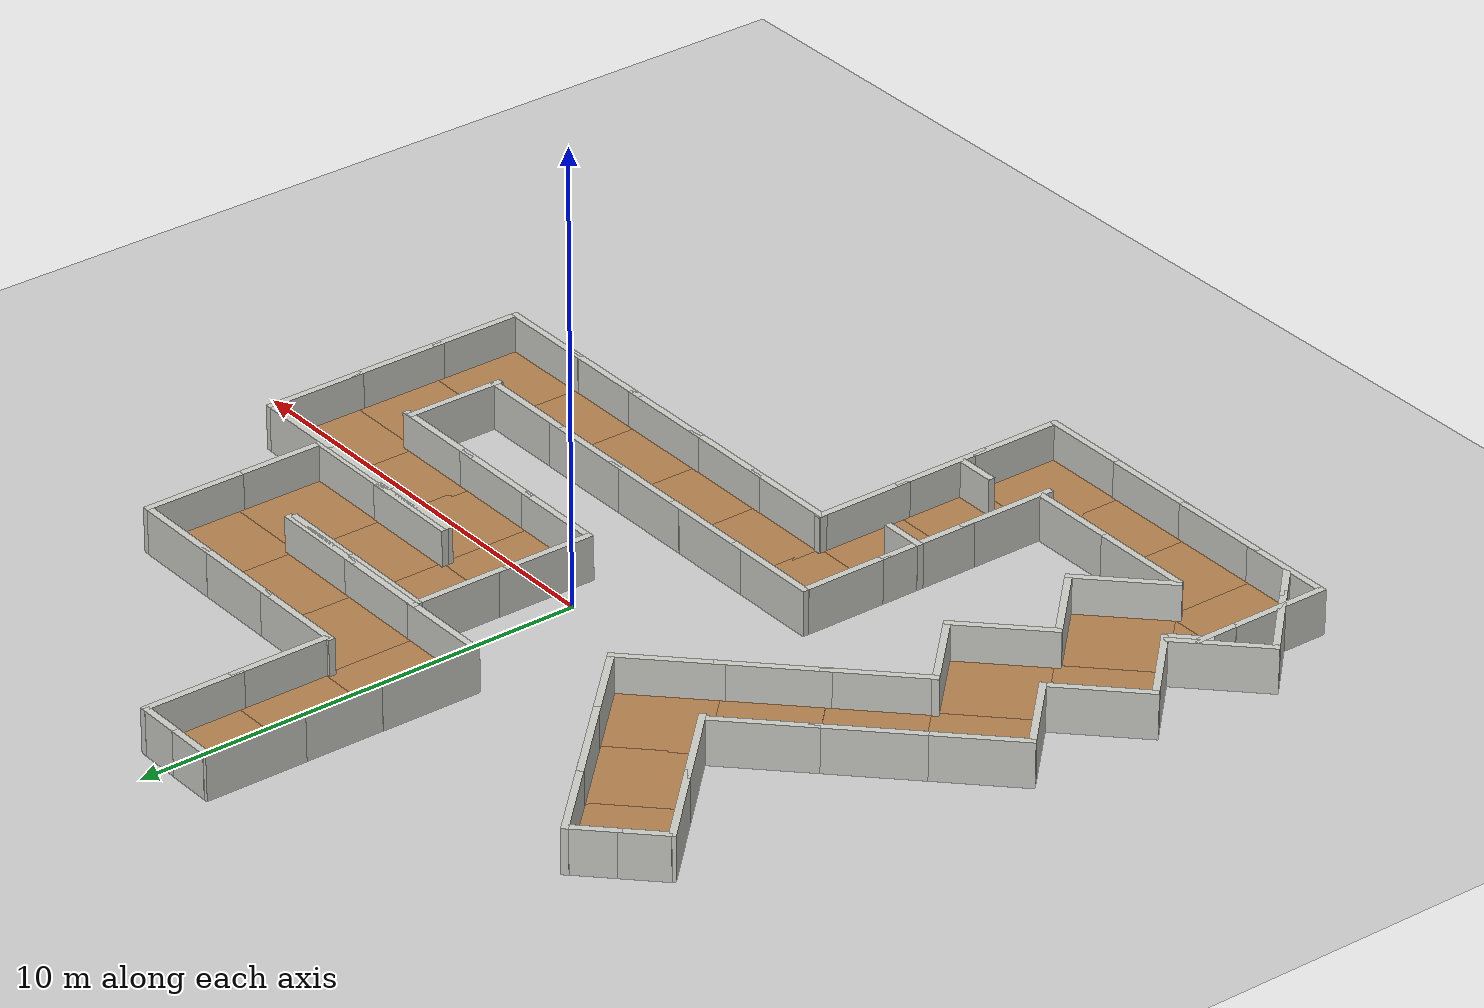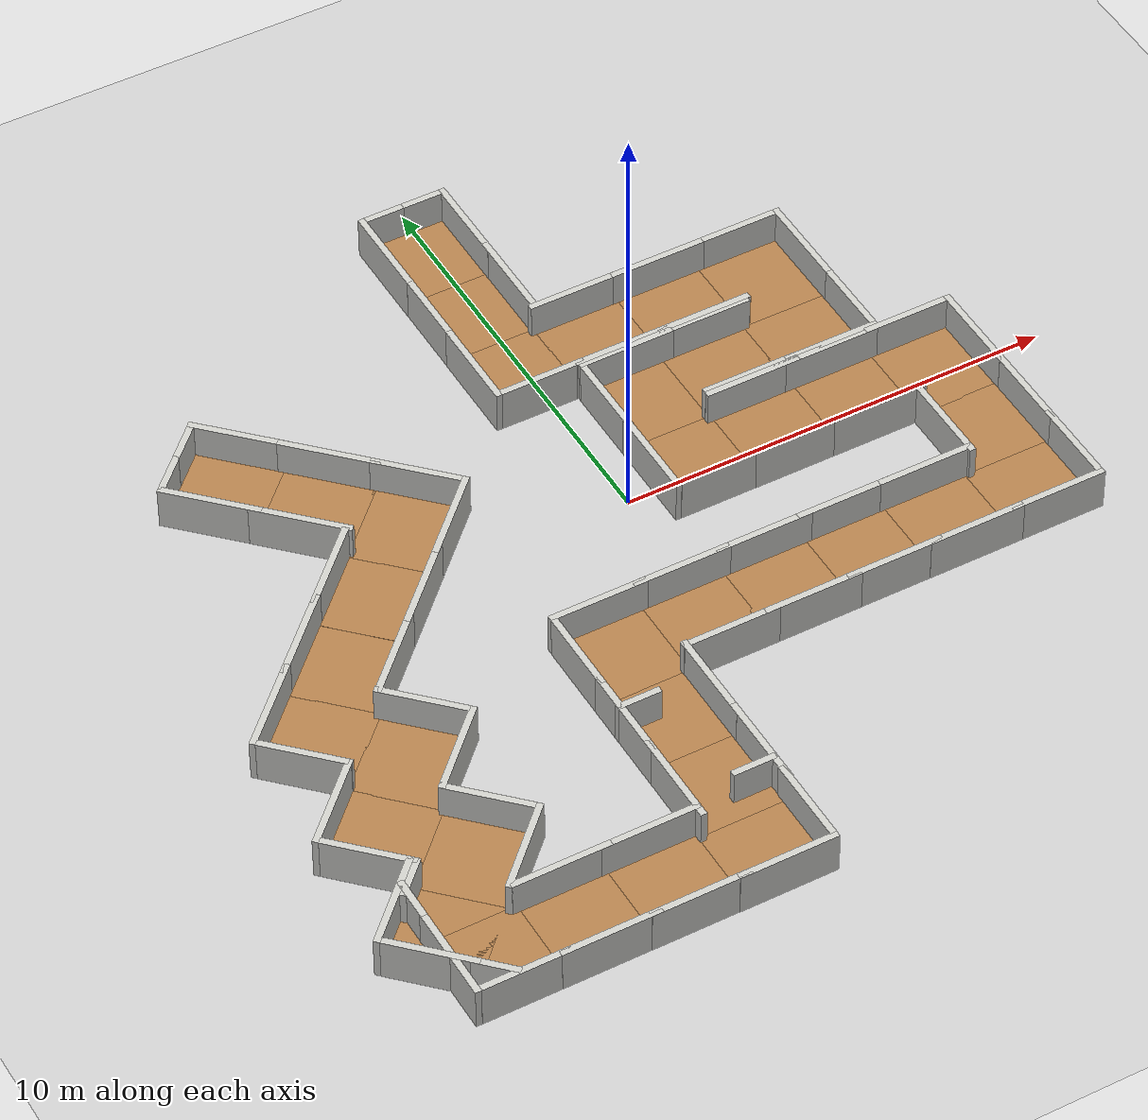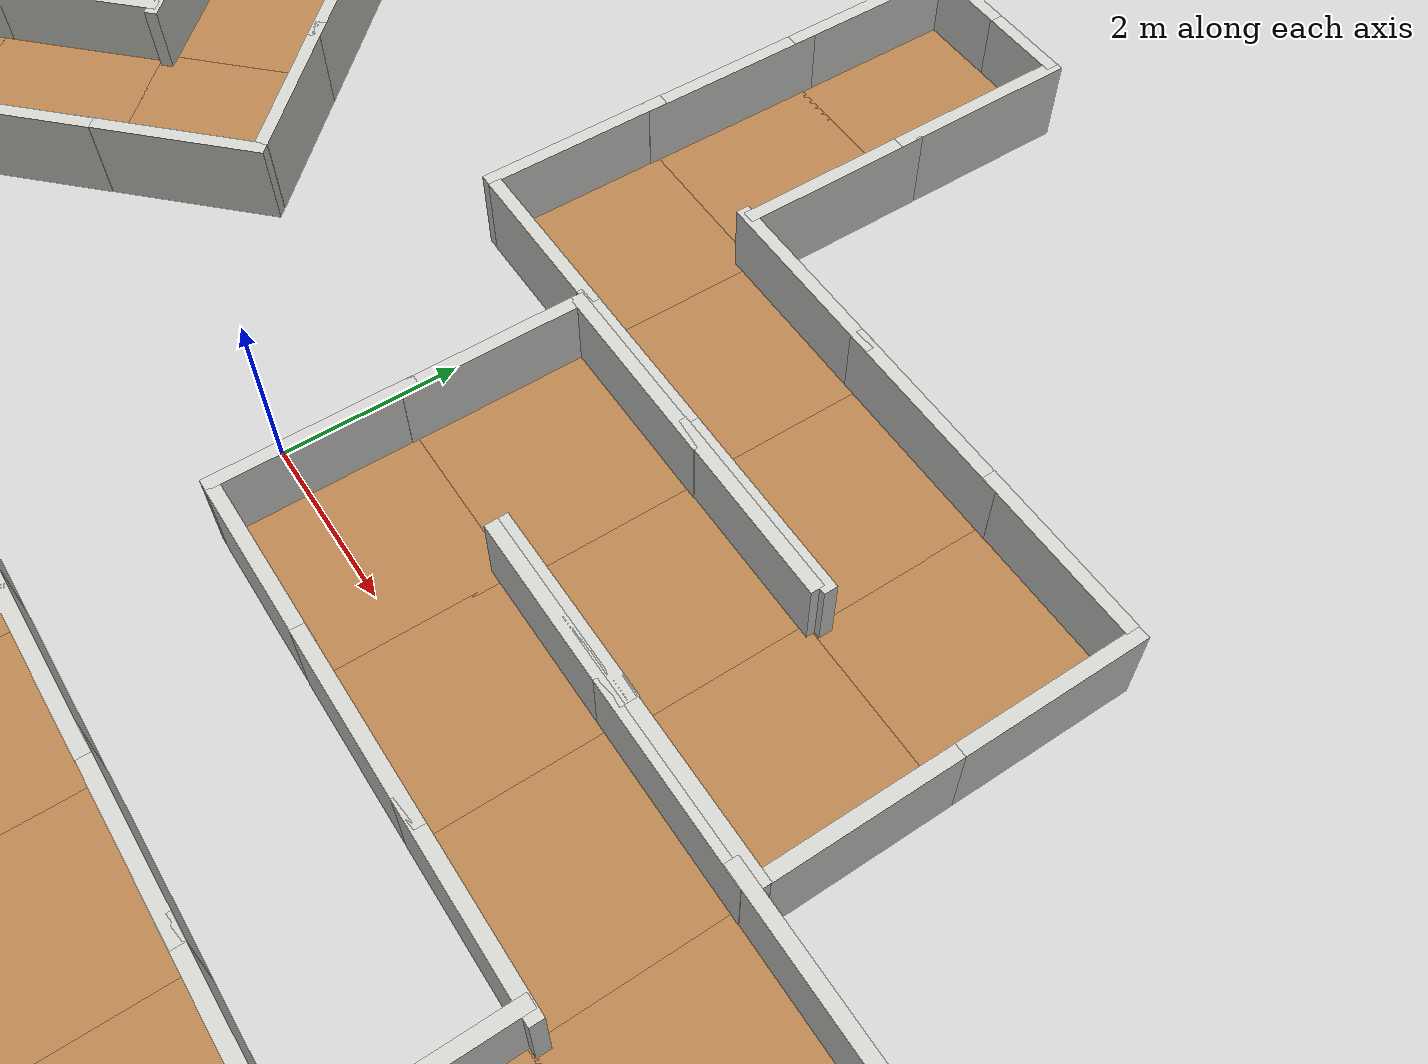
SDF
<sdf version="1.6">
 <world name="default">
  <light name="sun" type="directional">
   <pose>0 0 10 0 -0 0</pose>
   <diffuse>0.8 0.8 0.8 1</diffuse>
   <specular>0.2 0.2 0.2 1</specular>
   <attenuation>
    <range>1000</range>
    <constant>0.9</constant>
    <linear>0.01</linear>
    <quadratic>0.001</quadratic>
   </attenuation>
   <direction>-0.5 0.1 -0.9</direction>
  </light>
  <model name="ground_plane">
   <static>1</static>
   <link name="link">
    <collision name="collision">
     <geometry><plane><normal>0 0 1</normal><size>100 100</size></plane></geometry>
     <surface><friction><ode><mu>100</mu><mu2>50</mu2></ode></friction></surface>
    </collision>
    <visual name="visual">
     <cast_shadows>0</cast_shadows>
     <geometry><plane><normal>0 0 1</normal><size>100 100</size></plane></geometry>
     <material>
      <script><uri>file://media/materials/scripts/gazebo.material</uri><name>Gazebo/Grey</name></script>
     </material>
    </visual>
   </link>
  </model>
  <gravity>0 0 -9.8</gravity>
  <magnetic_field>6e-06 2.3e-05 -4.2e-05</magnetic_field>
  <atmosphere type="adiabatic"/>
  <physics name="default_physics" default="0" type="ode">
   <max_step_size>0.001</max_step_size>
   <real_time_factor>1</real_time_factor>
   <real_time_update_rate>1000</real_time_update_rate>
  </physics>
  <scene><ambient>0.4 0.4 0.4 1</ambient><background>0.7 0.7 0.7 1</background><shadows>1</shadows></scene>
  <spherical_coordinates>
   <surface_model>EARTH_WGS84</surface_model>
   <latitude_deg>0</latitude_deg>
   <longitude_deg>0</longitude_deg>
   <elevation>0</elevation>
   <heading_deg>0</heading_deg>
  </spherical_coordinates>
  <model name="pg_maze_straight">
   <pose>1.51595 -3.89785 0 0 -0 0</pose>
   <link name="Wall_0">
    <collision name="Wall_0_Collision">
     <geometry><box><size>2.01 2 0.2</size></box></geometry>
     <pose>0 0 0.1 0 -0 0</pose>
    </collision>
    <visual name="Wall_0_Visual">
     <pose>0 0 0.1 0 -0 0</pose>
     <geometry><box><size>2.01 2 0.2</size></box></geometry>
     <material>
      <script><uri>file://media/materials/scripts/gazebo.material</uri><name>Gazebo/Wood</name></script>
      <ambient>1 1 1 1</ambient>
     </material>
     <meta><layer>0</layer></meta>
    </visual>
    <pose>0.003 -0.001 0 0 -0 0</pose>
   </link>
   <link name="Wall_2">
    <collision name="Wall_2_Collision">
     <geometry><box><size>2.25 0.15 1</size></box></geometry>
     <pose>0 0 0.5 0 -0 0</pose>
    </collision>
    <visual name="Wall_2_Visual">
     <pose>0 0 0.5 0 -0 0</pose>
     <geometry><box><size>2.25 0.15 1</size></box></geometry>
     <material>
      <script><uri>file://media/materials/scripts/gazebo.material</uri><name>Gazebo/CeilingTiled</name></script>
      <ambient>0.996078 0.47451 0.0196078 1</ambient>
     </material>
     <meta><layer>0</layer></meta>
    </visual>
    <pose>-0.005 0.985 0 0 -0 0</pose>
   </link>
   <link name="Wall_4">
    <collision name="Wall_4_Collision">
     <geometry><box><size>2.25 0.15 1</size></box></geometry>
     <pose>0 0 0.5 0 -0 0</pose>
    </collision>
    <visual name="Wall_4_Visual">
     <pose>0 0 0.5 0 -0 0</pose>
     <geometry><box><size>2.25 0.15 1</size></box></geometry>
     <material>
      <script><uri>file://media/materials/scripts/gazebo.material</uri><name>Gazebo/CeilingTiled</name></script>
      <ambient>0.996078 0.47451 0.0196078 1</ambient>
     </material>
     <meta><layer>0</layer></meta>
    </visual>
    <pose>0.005 -0.985 0 0 -0 0</pose>
   </link>
   <static>1</static>
  </model>
  <model name="pg_maze_straight_0">
   <pose>-0.420246 -3.89882 0 0 -0 0</pose>
   <link name="Wall_0">
    <collision name="Wall_0_Collision">
     <geometry><box><size>2.01 2 0.2</size></box></geometry>
     <pose>0 0 0.1 0 -0 0</pose>
    </collision>
    <visual name="Wall_0_Visual">
     <pose>0 0 0.1 0 -0 0</pose>
     <geometry><box><size>2.01 2 0.2</size></box></geometry>
     <material>
      <script><uri>file://media/materials/scripts/gazebo.material</uri><name>Gazebo/Wood</name></script>
      <ambient>1 1 1 1</ambient>
     </material>
     <meta><layer>0</layer></meta>
    </visual>
    <pose>0.003 -0.001 0 0 -0 0</pose>
   </link>
   <link name="Wall_2">
    <collision name="Wall_2_Collision">
     <geometry><box><size>2.25 0.15 1</size></box></geometry>
     <pose>0 0 0.5 0 -0 0</pose>
    </collision>
    <visual name="Wall_2_Visual">
     <pose>0 0 0.5 0 -0 0</pose>
     <geometry><box><size>2.25 0.15 1</size></box></geometry>
     <material>
      <script><uri>file://media/materials/scripts/gazebo.material</uri><name>Gazebo/CeilingTiled</name></script>
      <ambient>0.996078 0.47451 0.0196078 1</ambient>
     </material>
     <meta><layer>0</layer></meta>
    </visual>
    <pose>-0.005 0.985 0 0 -0 0</pose>
   </link>
   <link name="Wall_4">
    <collision name="Wall_4_Collision">
     <geometry><box><size>2.25 0.15 1</size></box></geometry>
     <pose>0 0 0.5 0 -0 0</pose>
    </collision>
    <visual name="Wall_4_Visual">
     <pose>0 0 0.5 0 -0 0</pose>
     <geometry><box><size>2.25 0.15 1</size></box></geometry>
     <material>
      <script><uri>file://media/materials/scripts/gazebo.material</uri><name>Gazebo/CeilingTiled</name></script>
      <ambient>0.996078 0.47451 0.0196078 1</ambient>
     </material>
     <meta><layer>0</layer></meta>
    </visual>
    <pose>0.005 -0.985 0 0 -0 0</pose>
   </link>
   <static>1</static>
  </model>
  <model name="pg_maze_corner">
   <pose>-2.37432 -3.9093 0 0 -0 0</pose>
   <link name="Wall_0">
    <collision name="Wall_0_Collision">
     <geometry><box><size>2.01 2 0.2</size></box></geometry>
     <pose>0 0 0.1 0 -0 0</pose>
    </collision>
    <visual name="Wall_0_Visual">
     <pose>0 0 0.1 0 -0 0</pose>
     <geometry><box><size>2.01 2 0.2</size></box></geometry>
     <material>
      <script><uri>file://media/materials/scripts/gazebo.material</uri><name>Gazebo/Wood</name></script>
      <ambient>1 1 1 1</ambient>
     </material>
     <meta><layer>0</layer></meta>
    </visual>
    <pose>0.009575 0.005575 0 0 -0 0</pose>
   </link>
   <link name="Wall_2">
    <collision name="Wall_2_Collision">
     <geometry><box><size>2.25 0.15 1</size></box></geometry>
     <pose>0 0 0.5 0 -0 0</pose>
    </collision>
    <visual name="Wall_2_Visual">
     <pose>0 0 0.5 0 -0 0</pose>
     <geometry><box><size>2.25 0.15 1</size></box></geometry>
     <material>
      <script><uri>file://media/materials/scripts/gazebo.material</uri><name>Gazebo/CeilingTiled</name></script>
      <ambient>0.996078 0.47451 0.0196078 1</ambient>
     </material>
     <meta><layer>0</layer></meta>
    </visual>
    <pose>0.001575 0.991575 0 0 -0 0</pose>
   </link>
   <link name="Wall_4">
    <collision name="Wall_4_Collision">
     <geometry><box><size>2 0.15 1</size></box></geometry>
     <pose>0 0 0.5 0 -0 0</pose>
    </collision>
    <visual name="Wall_4_Visual">
     <pose>0 0 0.5 0 -0 0</pose>
     <geometry><box><size>2 0.15 1</size></box></geometry>
     <material>
      <script><uri>file://media/materials/scripts/gazebo.material</uri><name>Gazebo/CeilingTiled</name></script>
      <ambient>0.996078 0.47451 0.0196078 1</ambient>
     </material>
     <meta><layer>0</layer></meta>
    </visual>
    <pose>-1.05157 -0.066575 0 0 -0 1.5708</pose>
   </link>
   <static>1</static>
  </model>
  <model name="pg_maze_straight_1">
   <pose>-2.44128 -5.90392 0 0 -0 1.5708</pose>
   <link name="Wall_0">
    <collision name="Wall_0_Collision">
     <geometry><box><size>2.01 2 0.2</size></box></geometry>
     <pose>0 0 0.1 0 -0 0</pose>
    </collision>
    <visual name="Wall_0_Visual">
     <pose>0 0 0.1 0 -0 0</pose>
     <geometry><box><size>2.01 2 0.2</size></box></geometry>
     <material>
      <script><uri>file://media/materials/scripts/gazebo.material</uri><name>Gazebo/Wood</name></script>
      <ambient>1 1 1 1</ambient>
     </material>
     <meta><layer>0</layer></meta>
    </visual>
    <pose>0.003 -0.001 0 0 -0 0</pose>
   </link>
   <link name="Wall_2">
    <collision name="Wall_2_Collision">
     <geometry><box><size>2.25 0.15 1</size></box></geometry>
     <pose>0 0 0.5 0 -0 0</pose>
    </collision>
    <visual name="Wall_2_Visual">
     <pose>0 0 0.5 0 -0 0</pose>
     <geometry><box><size>2.25 0.15 1</size></box></geometry>
     <material>
      <script><uri>file://media/materials/scripts/gazebo.material</uri><name>Gazebo/CeilingTiled</name></script>
      <ambient>0.996078 0.47451 0.0196078 1</ambient>
     </material>
     <meta><layer>0</layer></meta>
    </visual>
    <pose>-0.005 0.985 0 0 -0 0</pose>
   </link>
   <link name="Wall_4">
    <collision name="Wall_4_Collision">
     <geometry><box><size>2.25 0.15 1</size></box></geometry>
     <pose>0 0 0.5 0 -0 0</pose>
    </collision>
    <visual name="Wall_4_Visual">
     <pose>0 0 0.5 0 -0 0</pose>
     <geometry><box><size>2.25 0.15 1</size></box></geometry>
     <material>
      <script><uri>file://media/materials/scripts/gazebo.material</uri><name>Gazebo/CeilingTiled</name></script>
      <ambient>0.996078 0.47451 0.0196078 1</ambient>
     </material>
     <meta><layer>0</layer></meta>
    </visual>
    <pose>0.005 -0.985 0 0 -0 0</pose>
   </link>
   <static>1</static>
  </model>
  <model name="pg_maze_straight_1_clone">
   <pose>-2.44005 -7.87477 0 0 -0 1.5708</pose>
   <link name="Wall_0">
    <collision name="Wall_0_Collision">
     <geometry><box><size>2.01 2 0.2</size></box></geometry>
     <pose>0 0 0.1 0 -0 0</pose>
    </collision>
    <visual name="Wall_0_Visual">
     <pose>0 0 0.1 0 -0 0</pose>
     <geometry><box><size>2.01 2 0.2</size></box></geometry>
     <material>
      <script><uri>file://media/materials/scripts/gazebo.material</uri><name>Gazebo/Wood</name></script>
      <ambient>1 1 1 1</ambient>
     </material>
     <meta><layer>0</layer></meta>
    </visual>
    <pose>0.003 -0.001 0 0 -0 0</pose>
   </link>
   <link name="Wall_2">
    <collision name="Wall_2_Collision">
     <geometry><box><size>2.25 0.15 1</size></box></geometry>
     <pose>0 0 0.5 0 -0 0</pose>
    </collision>
    <visual name="Wall_2_Visual">
     <pose>0 0 0.5 0 -0 0</pose>
     <geometry><box><size>2.25 0.15 1</size></box></geometry>
     <material>
      <script><uri>file://media/materials/scripts/gazebo.material</uri><name>Gazebo/CeilingTiled</name></script>
      <ambient>0.996078 0.47451 0.0196078 1</ambient>
     </material>
     <meta><layer>0</layer></meta>
    </visual>
    <pose>-0.005 0.985 0 0 -0 0</pose>
   </link>
   <link name="Wall_4">
    <collision name="Wall_4_Collision">
     <geometry><box><size>2.25 0.15 1</size></box></geometry>
     <pose>0 0 0.5 0 -0 0</pose>
    </collision>
    <visual name="Wall_4_Visual">
     <pose>0 0 0.5 0 -0 0</pose>
     <geometry><box><size>2.25 0.15 1</size></box></geometry>
     <material>
      <script><uri>file://media/materials/scripts/gazebo.material</uri><name>Gazebo/CeilingTiled</name></script>
      <ambient>0.996078 0.47451 0.0196078 1</ambient>
     </material>
     <meta><layer>0</layer></meta>
    </visual>
    <pose>0.005 -0.985 0 0 -0 0</pose>
   </link>
   <static>1</static>
  </model>
  <model name="pg_maze_corner_0">
   <pose>-2.51891 -9.72043 0 0 0 -3.14159</pose>
   <link name="Wall_0">
    <collision name="Wall_0_Collision">
     <geometry><box><size>2.01 2 0.2</size></box></geometry>
     <pose>0 0 0.1 0 -0 0</pose>
    </collision>
    <visual name="Wall_0_Visual">
     <pose>0 0 0.1 0 -0 0</pose>
     <geometry><box><size>2.01 2 0.2</size></box></geometry>
     <material>
      <script><uri>file://media/materials/scripts/gazebo.material</uri><name>Gazebo/Wood</name></script>
      <ambient>1 1 1 1</ambient>
     </material>
     <meta><layer>0</layer></meta>
    </visual>
    <pose>0.009575 0.005575 0 0 -0 0</pose>
   </link>
   <link name="Wall_2">
    <collision name="Wall_2_Collision">
     <geometry><box><size>2.25 0.15 1</size></box></geometry>
     <pose>0 0 0.5 0 -0 0</pose>
    </collision>
    <visual name="Wall_2_Visual">
     <pose>0 0 0.5 0 -0 0</pose>
     <geometry><box><size>2.25 0.15 1</size></box></geometry>
     <material>
      <script><uri>file://media/materials/scripts/gazebo.material</uri><name>Gazebo/CeilingTiled</name></script>
      <ambient>0.996078 0.47451 0.0196078 1</ambient>
     </material>
     <meta><layer>0</layer></meta>
    </visual>
    <pose>0.001575 0.991575 0 0 -0 0</pose>
   </link>
   <link name="Wall_4">
    <collision name="Wall_4_Collision">
     <geometry><box><size>2 0.15 1</size></box></geometry>
     <pose>0 0 0.5 0 -0 0</pose>
    </collision>
    <visual name="Wall_4_Visual">
     <pose>0 0 0.5 0 -0 0</pose>
     <geometry><box><size>2 0.15 1</size></box></geometry>
     <material>
      <script><uri>file://media/materials/scripts/gazebo.material</uri><name>Gazebo/CeilingTiled</name></script>
      <ambient>0.996078 0.47451 0.0196078 1</ambient>
     </material>
     <meta><layer>0</layer></meta>
    </visual>
    <pose>-1.05157 -0.066575 0 0 -0 1.5708</pose>
   </link>
   <static>1</static>
  </model>
  <model name="pg_maze_obstacle">
   <pose>-3.00422 -5.68975 0 0 -0 0</pose>
   <link name="Wall_2">
    <collision name="Wall_2_Collision">
     <geometry><box><size>1 0.15 1</size></box></geometry>
     <pose>0 0 0.5 0 -0 0</pose>
    </collision>
    <visual name="Wall_2_Visual">
     <pose>0 0 0.5 0 -0 0</pose>
     <geometry><box><size>1 0.15 1</size></box></geometry>
     <material>
      <script><uri>file://media/materials/scripts/gazebo.material</uri><name>Gazebo/CeilingTiled</name></script>
      <ambient>0.996078 0.47451 0.0196078 1</ambient>
     </material>
     <meta><layer>0</layer></meta>
    </visual>
   </link>
   <static>1</static>
  </model>
  <model name="pg_maze_obstacle_0">
   <pose>-1.9083 -8.35012 0 0 -0 0</pose>
   <link name="Wall_2">
    <collision name="Wall_2_Collision">
     <geometry><box><size>1 0.15 1</size></box></geometry>
     <pose>0 0 0.5 0 -0 0</pose>
    </collision>
    <visual name="Wall_2_Visual">
     <pose>0 0 0.5 0 -0 0</pose>
     <geometry><box><size>1 0.15 1</size></box></geometry>
     <material>
      <script><uri>file://media/materials/scripts/gazebo.material</uri><name>Gazebo/CeilingTiled</name></script>
      <ambient>0.996078 0.47451 0.0196078 1</ambient>
     </material>
     <meta><layer>0</layer></meta>
    </visual>
   </link>
   <static>1</static>
  </model>
  <model name="pg_maze_straight_2">
   <pose>3.46221 -3.89407 0 0 -0 0</pose>
   <link name="Wall_0">
    <collision name="Wall_0_Collision">
     <geometry><box><size>2.01 2 0.2</size></box></geometry>
     <pose>0 0 0.1 0 -0 0</pose>
    </collision>
    <visual name="Wall_0_Visual">
     <pose>0 0 0.1 0 -0 0</pose>
     <geometry><box><size>2.01 2 0.2</size></box></geometry>
     <material>
      <script><uri>file://media/materials/scripts/gazebo.material</uri><name>Gazebo/Wood</name></script>
      <ambient>1 1 1 1</ambient>
     </material>
     <meta><layer>0</layer></meta>
    </visual>
    <pose>0.003 -0.001 0 0 -0 0</pose>
   </link>
   <link name="Wall_2">
    <collision name="Wall_2_Collision">
     <geometry><box><size>2.25 0.15 1</size></box></geometry>
     <pose>0 0 0.5 0 -0 0</pose>
    </collision>
    <visual name="Wall_2_Visual">
     <pose>0 0 0.5 0 -0 0</pose>
     <geometry><box><size>2.25 0.15 1</size></box></geometry>
     <material>
      <script><uri>file://media/materials/scripts/gazebo.material</uri><name>Gazebo/CeilingTiled</name></script>
      <ambient>0.996078 0.47451 0.0196078 1</ambient>
     </material>
     <meta><layer>0</layer></meta>
    </visual>
    <pose>-0.005 0.985 0 0 -0 0</pose>
   </link>
   <link name="Wall_4">
    <collision name="Wall_4_Collision">
     <geometry><box><size>2.25 0.15 1</size></box></geometry>
     <pose>0 0 0.5 0 -0 0</pose>
    </collision>
    <visual name="Wall_4_Visual">
     <pose>0 0 0.5 0 -0 0</pose>
     <geometry><box><size>2.25 0.15 1</size></box></geometry>
     <material>
      <script><uri>file://media/materials/scripts/gazebo.material</uri><name>Gazebo/CeilingTiled</name></script>
      <ambient>0.996078 0.47451 0.0196078 1</ambient>
     </material>
     <meta><layer>0</layer></meta>
    </visual>
    <pose>0.005 -0.985 0 0 -0 0</pose>
   </link>
   <static>1</static>
  </model>
  <model name="pg_maze_straight_3">
   <pose>5.41322 -3.89645 0 0 -0 0</pose>
   <link name="Wall_0">
    <collision name="Wall_0_Collision">
     <geometry><box><size>2.01 2 0.2</size></box></geometry>
     <pose>0 0 0.1 0 -0 0</pose>
    </collision>
    <visual name="Wall_0_Visual">
     <pose>0 0 0.1 0 -0 0</pose>
     <geometry><box><size>2.01 2 0.2</size></box></geometry>
     <material>
      <script><uri>file://media/materials/scripts/gazebo.material</uri><name>Gazebo/Wood</name></script>
      <ambient>1 1 1 1</ambient>
     </material>
     <meta><layer>0</layer></meta>
    </visual>
    <pose>0.003 -0.001 0 0 -0 0</pose>
   </link>
   <link name="Wall_2">
    <collision name="Wall_2_Collision">
     <geometry><box><size>2.25 0.15 1</size></box></geometry>
     <pose>0 0 0.5 0 -0 0</pose>
    </collision>
    <visual name="Wall_2_Visual">
     <pose>0 0 0.5 0 -0 0</pose>
     <geometry><box><size>2.25 0.15 1</size></box></geometry>
     <material>
      <script><uri>file://media/materials/scripts/gazebo.material</uri><name>Gazebo/CeilingTiled</name></script>
      <ambient>0.996078 0.47451 0.0196078 1</ambient>
     </material>
     <meta><layer>0</layer></meta>
    </visual>
    <pose>-0.005 0.985 0 0 -0 0</pose>
   </link>
   <link name="Wall_4">
    <collision name="Wall_4_Collision">
     <geometry><box><size>2.25 0.15 1</size></box></geometry>
     <pose>0 0 0.5 0 -0 0</pose>
    </collision>
    <visual name="Wall_4_Visual">
     <pose>0 0 0.5 0 -0 0</pose>
     <geometry><box><size>2.25 0.15 1</size></box></geometry>
     <material>
      <script><uri>file://media/materials/scripts/gazebo.material</uri><name>Gazebo/CeilingTiled</name></script>
      <ambient>0.996078 0.47451 0.0196078 1</ambient>
     </material>
     <meta><layer>0</layer></meta>
    </visual>
    <pose>0.005 -0.985 0 0 -0 0</pose>
   </link>
   <static>1</static>
  </model>
  <model name="pg_maze_corner_1">
   <pose>7.39579 -3.88557 0 0 -0 3.14159</pose>
   <link name="Wall_0">
    <collision name="Wall_0_Collision">
     <geometry><box><size>2.01 2 0.2</size></box></geometry>
     <pose>0 0 0.1 0 -0 0</pose>
    </collision>
    <visual name="Wall_0_Visual">
     <pose>0 0 0.1 0 -0 0</pose>
     <geometry><box><size>2.01 2 0.2</size></box></geometry>
     <material>
      <script><uri>file://media/materials/scripts/gazebo.material</uri><name>Gazebo/Wood</name></script>
      <ambient>1 1 1 1</ambient>
     </material>
     <meta><layer>0</layer></meta>
    </visual>
    <pose>0.009575 0.005575 0 0 -0 0</pose>
   </link>
   <link name="Wall_2">
    <collision name="Wall_2_Collision">
     <geometry><box><size>2.25 0.15 1</size></box></geometry>
     <pose>0 0 0.5 0 -0 0</pose>
    </collision>
    <visual name="Wall_2_Visual">
     <pose>0 0 0.5 0 -0 0</pose>
     <geometry><box><size>2.25 0.15 1</size></box></geometry>
     <material>
      <script><uri>file://media/materials/scripts/gazebo.material</uri><name>Gazebo/CeilingTiled</name></script>
      <ambient>0.996078 0.47451 0.0196078 1</ambient>
     </material>
     <meta><layer>0</layer></meta>
    </visual>
    <pose>0.001575 0.991575 0 0 -0 0</pose>
   </link>
   <link name="Wall_4">
    <collision name="Wall_4_Collision">
     <geometry><box><size>2 0.15 1</size></box></geometry>
     <pose>0 0 0.5 0 -0 0</pose>
    </collision>
    <visual name="Wall_4_Visual">
     <pose>0 0 0.5 0 -0 0</pose>
     <geometry><box><size>2 0.15 1</size></box></geometry>
     <material>
      <script><uri>file://media/materials/scripts/gazebo.material</uri><name>Gazebo/CeilingTiled</name></script>
      <ambient>0.996078 0.47451 0.0196078 1</ambient>
     </material>
     <meta><layer>0</layer></meta>
    </visual>
    <pose>-1.05157 -0.066575 0 0 -0 1.5708</pose>
   </link>
   <static>1</static>
  </model>
  <model name="pg_maze_straight_4">
   <pose>7.46235 -1.928 0 0 0 -1.5708</pose>
   <link name="Wall_0">
    <collision name="Wall_0_Collision">
     <geometry><box><size>2.01 2 0.2</size></box></geometry>
     <pose>0 0 0.1 0 -0 0</pose>
    </collision>
    <visual name="Wall_0_Visual">
     <pose>0 0 0.1 0 -0 0</pose>
     <geometry><box><size>2.01 2 0.2</size></box></geometry>
     <material>
      <script><uri>file://media/materials/scripts/gazebo.material</uri><name>Gazebo/Wood</name></script>
      <ambient>1 1 1 1</ambient>
     </material>
     <meta><layer>0</layer></meta>
    </visual>
    <pose>0.003 -0.001 0 0 -0 0</pose>
   </link>
   <link name="Wall_2">
    <collision name="Wall_2_Collision">
     <geometry><box><size>2.25 0.15 1</size></box></geometry>
     <pose>0 0 0.5 0 -0 0</pose>
    </collision>
    <visual name="Wall_2_Visual">
     <pose>0 0 0.5 0 -0 0</pose>
     <geometry><box><size>2.25 0.15 1</size></box></geometry>
     <material>
      <script><uri>file://media/materials/scripts/gazebo.material</uri><name>Gazebo/CeilingTiled</name></script>
      <ambient>0.996078 0.47451 0.0196078 1</ambient>
     </material>
     <meta><layer>0</layer></meta>
    </visual>
    <pose>-0.005 0.985 0 0 -0 0</pose>
   </link>
   <link name="Wall_4">
    <collision name="Wall_4_Collision">
     <geometry><box><size>2.25 0.15 1</size></box></geometry>
     <pose>0 0 0.5 0 -0 0</pose>
    </collision>
    <visual name="Wall_4_Visual">
     <pose>0 0 0.5 0 -0 0</pose>
     <geometry><box><size>2.25 0.15 1</size></box></geometry>
     <material>
      <script><uri>file://media/materials/scripts/gazebo.material</uri><name>Gazebo/CeilingTiled</name></script>
      <ambient>0.996078 0.47451 0.0196078 1</ambient>
     </material>
     <meta><layer>0</layer></meta>
    </visual>
    <pose>0.005 -0.985 0 0 -0 0</pose>
   </link>
   <static>1</static>
  </model>
  <model name="pg_maze_corner_0_clone">
   <pose>7.45381 0.055757 0 0 0 -1.57079</pose>
   <link name="Wall_0">
    <collision name="Wall_0_Collision">
     <geometry><box><size>2.01 2 0.2</size></box></geometry>
     <pose>0 0 0.1 0 -0 0</pose>
    </collision>
    <visual name="Wall_0_Visual">
     <pose>0 0 0.1 0 -0 0</pose>
     <geometry><box><size>2.01 2 0.2</size></box></geometry>
     <material>
      <script><uri>file://media/materials/scripts/gazebo.material</uri><name>Gazebo/Wood</name></script>
      <ambient>1 1 1 1</ambient>
     </material>
     <meta><layer>0</layer></meta>
    </visual>
    <pose>0.009575 0.005575 0 0 -0 0</pose>
   </link>
   <link name="Wall_2">
    <collision name="Wall_2_Collision">
     <geometry><box><size>2.25 0.15 1</size></box></geometry>
     <pose>0 0 0.5 0 -0 0</pose>
    </collision>
    <visual name="Wall_2_Visual">
     <pose>0 0 0.5 0 -0 0</pose>
     <geometry><box><size>2.25 0.15 1</size></box></geometry>
     <material>
      <script><uri>file://media/materials/scripts/gazebo.material</uri><name>Gazebo/CeilingTiled</name></script>
      <ambient>0.996078 0.47451 0.0196078 1</ambient>
     </material>
     <meta><layer>0</layer></meta>
    </visual>
    <pose>0.001575 0.991575 0 0 -0 0</pose>
   </link>
   <link name="Wall_4">
    <collision name="Wall_4_Collision">
     <geometry><box><size>2 0.15 1</size></box></geometry>
     <pose>0 0 0.5 0 -0 0</pose>
    </collision>
    <visual name="Wall_4_Visual">
     <pose>0 0 0.5 0 -0 0</pose>
     <geometry><box><size>2 0.15 1</size></box></geometry>
     <material>
      <script><uri>file://media/materials/scripts/gazebo.material</uri><name>Gazebo/CeilingTiled</name></script>
      <ambient>0.996078 0.47451 0.0196078 1</ambient>
     </material>
     <meta><layer>0</layer></meta>
    </visual>
    <pose>-1.05157 -0.066575 0 0 -0 1.5708</pose>
   </link>
   <static>1</static>
  </model>
  <model name="pg_maze_straight_2_clone">
   <pose>5.52215 0.11779 0 0 -0 0</pose>
   <link name="Wall_0">
    <collision name="Wall_0_Collision">
     <geometry><box><size>2.01 2 0.2</size></box></geometry>
     <pose>0 0 0.1 0 -0 0</pose>
    </collision>
    <visual name="Wall_0_Visual">
     <pose>0 0 0.1 0 -0 0</pose>
     <geometry><box><size>2.01 2 0.2</size></box></geometry>
     <material>
      <script><uri>file://media/materials/scripts/gazebo.material</uri><name>Gazebo/Wood</name></script>
      <ambient>1 1 1 1</ambient>
     </material>
     <meta><layer>0</layer></meta>
    </visual>
    <pose>0.003 -0.001 0 0 -0 0</pose>
   </link>
   <link name="Wall_2">
    <collision name="Wall_2_Collision">
     <geometry><box><size>2.25 0.15 1</size></box></geometry>
     <pose>0 0 0.5 0 -0 0</pose>
    </collision>
    <visual name="Wall_2_Visual">
     <pose>0 0 0.5 0 -0 0</pose>
     <geometry><box><size>2.25 0.15 1</size></box></geometry>
     <material>
      <script><uri>file://media/materials/scripts/gazebo.material</uri><name>Gazebo/CeilingTiled</name></script>
      <ambient>0.996078 0.47451 0.0196078 1</ambient>
     </material>
     <meta><layer>0</layer></meta>
    </visual>
    <pose>-0.005 0.985 0 0 -0 0</pose>
   </link>
   <link name="Wall_4">
    <collision name="Wall_4_Collision">
     <geometry><box><size>2.25 0.15 1</size></box></geometry>
     <pose>0 0 0.5 0 -0 0</pose>
    </collision>
    <visual name="Wall_4_Visual">
     <pose>0 0 0.5 0 -0 0</pose>
     <geometry><box><size>2.25 0.15 1</size></box></geometry>
     <material>
      <script><uri>file://media/materials/scripts/gazebo.material</uri><name>Gazebo/CeilingTiled</name></script>
      <ambient>0.996078 0.47451 0.0196078 1</ambient>
     </material>
     <meta><layer>0</layer></meta>
    </visual>
    <pose>0.005 -0.985 0 0 -0 0</pose>
   </link>
   <static>1</static>
  </model>
  <model name="pg_maze_straight_2_clone_0">
   <pose>3.62192 0.118087 0 0 -0 0</pose>
   <link name="Wall_0">
    <collision name="Wall_0_Collision">
     <geometry><box><size>2.01 2 0.2</size></box></geometry>
     <pose>0 0 0.1 0 -0 0</pose>
    </collision>
    <visual name="Wall_0_Visual">
     <pose>0 0 0.1 0 -0 0</pose>
     <geometry><box><size>2.01 2 0.2</size></box></geometry>
     <material>
      <script><uri>file://media/materials/scripts/gazebo.material</uri><name>Gazebo/Wood</name></script>
      <ambient>1 1 1 1</ambient>
     </material>
     <meta><layer>0</layer></meta>
    </visual>
    <pose>0.003 -0.001 0 0 -0 0</pose>
   </link>
   <link name="Wall_2">
    <collision name="Wall_2_Collision">
     <geometry><box><size>2.25 0.15 1</size></box></geometry>
     <pose>0 0 0.5 0 -0 0</pose>
    </collision>
    <visual name="Wall_2_Visual">
     <pose>0 0 0.5 0 -0 0</pose>
     <geometry><box><size>2.25 0.15 1</size></box></geometry>
     <material>
      <script><uri>file://media/materials/scripts/gazebo.material</uri><name>Gazebo/CeilingTiled</name></script>
      <ambient>0.996078 0.47451 0.0196078 1</ambient>
     </material>
     <meta><layer>0</layer></meta>
    </visual>
    <pose>-0.005 0.985 0 0 -0 0</pose>
   </link>
   <link name="Wall_4">
    <collision name="Wall_4_Collision">
     <geometry><box><size>2.25 0.15 1</size></box></geometry>
     <pose>0 0 0.5 0 -0 0</pose>
    </collision>
    <visual name="Wall_4_Visual">
     <pose>0 0 0.5 0 -0 0</pose>
     <geometry><box><size>2.25 0.15 1</size></box></geometry>
     <material>
      <script><uri>file://media/materials/scripts/gazebo.material</uri><name>Gazebo/CeilingTiled</name></script>
      <ambient>0.996078 0.47451 0.0196078 1</ambient>
     </material>
     <meta><layer>0</layer></meta>
    </visual>
    <pose>0.005 -0.985 0 0 -0 0</pose>
   </link>
   <static>1</static>
  </model>
  <model name="pg_maze_corner_clone">
   <pose>1.65438 0.188296 0 0 -0 1.5708</pose>
   <link name="Wall_0">
    <collision name="Wall_0_Collision">
     <geometry><box><size>2.01 2 0.2</size></box></geometry>
     <pose>0 0 0.1 0 -0 0</pose>
    </collision>
    <visual name="Wall_0_Visual">
     <pose>0 0 0.1 0 -0 0</pose>
     <geometry><box><size>2.01 2 0.2</size></box></geometry>
     <material>
      <script><uri>file://media/materials/scripts/gazebo.material</uri><name>Gazebo/Wood</name></script>
      <ambient>1 1 1 1</ambient>
     </material>
     <meta><layer>0</layer></meta>
    </visual>
    <pose>0.009575 0.005575 0 0 -0 0</pose>
   </link>
   <link name="Wall_2">
    <collision name="Wall_2_Collision">
     <geometry><box><size>2.25 0.15 1</size></box></geometry>
     <pose>0 0 0.5 0 -0 0</pose>
    </collision>
    <visual name="Wall_2_Visual">
     <pose>0 0 0.5 0 -0 0</pose>
     <geometry><box><size>2.25 0.15 1</size></box></geometry>
     <material>
      <script><uri>file://media/materials/scripts/gazebo.material</uri><name>Gazebo/CeilingTiled</name></script>
      <ambient>0.996078 0.47451 0.0196078 1</ambient>
     </material>
     <meta><layer>0</layer></meta>
    </visual>
    <pose>0.001575 0.991575 0 0 -0 0</pose>
   </link>
   <link name="Wall_4">
    <collision name="Wall_4_Collision">
     <geometry><box><size>2 0.15 1</size></box></geometry>
     <pose>0 0 0.5 0 -0 0</pose>
    </collision>
    <visual name="Wall_4_Visual">
     <pose>0 0 0.5 0 -0 0</pose>
     <geometry><box><size>2 0.15 1</size></box></geometry>
     <material>
      <script><uri>file://media/materials/scripts/gazebo.material</uri><name>Gazebo/CeilingTiled</name></script>
      <ambient>0.996078 0.47451 0.0196078 1</ambient>
     </material>
     <meta><layer>0</layer></meta>
    </visual>
    <pose>-1.05157 -0.066575 0 0 -0 1.5708</pose>
   </link>
   <static>1</static>
  </model>
  <model name="pg_maze_corner_clone_0">
   <pose>1.72046 2.18253 0 0 -0 0</pose>
   <link name="Wall_0">
    <collision name="Wall_0_Collision">
     <geometry><box><size>2.01 2 0.2</size></box></geometry>
     <pose>0 0 0.1 0 -0 0</pose>
    </collision>
    <visual name="Wall_0_Visual">
     <pose>0 0 0.1 0 -0 0</pose>
     <geometry><box><size>2.01 2 0.2</size></box></geometry>
     <material>
      <script><uri>file://media/materials/scripts/gazebo.material</uri><name>Gazebo/Wood</name></script>
      <ambient>1 1 1 1</ambient>
     </material>
     <meta><layer>0</layer></meta>
    </visual>
    <pose>0.009575 0.005575 0 0 -0 0</pose>
   </link>
   <link name="Wall_2">
    <collision name="Wall_2_Collision">
     <geometry><box><size>2.25 0.15 1</size></box></geometry>
     <pose>0 0 0.5 0 -0 0</pose>
    </collision>
    <visual name="Wall_2_Visual">
     <pose>0 0 0.5 0 -0 0</pose>
     <geometry><box><size>2.25 0.15 1</size></box></geometry>
     <material>
      <script><uri>file://media/materials/scripts/gazebo.material</uri><name>Gazebo/CeilingTiled</name></script>
      <ambient>0.996078 0.47451 0.0196078 1</ambient>
     </material>
     <meta><layer>0</layer></meta>
    </visual>
    <pose>0.001575 0.991575 0 0 -0 0</pose>
   </link>
   <link name="Wall_4">
    <collision name="Wall_4_Collision">
     <geometry><box><size>2 0.15 1</size></box></geometry>
     <pose>0 0 0.5 0 -0 0</pose>
    </collision>
    <visual name="Wall_4_Visual">
     <pose>0 0 0.5 0 -0 0</pose>
     <geometry><box><size>2 0.15 1</size></box></geometry>
     <material>
      <script><uri>file://media/materials/scripts/gazebo.material</uri><name>Gazebo/CeilingTiled</name></script>
      <ambient>0.996078 0.47451 0.0196078 1</ambient>
     </material>
     <meta><layer>0</layer></meta>
    </visual>
    <pose>-1.05157 -0.066575 0 0 -0 1.5708</pose>
   </link>
   <static>1</static>
  </model>
  <model name="pg_maze_straight_2_clone_clone">
   <pose>3.61056 2.1969 0 0 -0 0</pose>
   <link name="Wall_0">
    <collision name="Wall_0_Collision">
     <geometry><box><size>2.01 2 0.2</size></box></geometry>
     <pose>0 0 0.1 0 -0 0</pose>
    </collision>
    <visual name="Wall_0_Visual">
     <pose>0 0 0.1 0 -0 0</pose>
     <geometry><box><size>2.01 2 0.2</size></box></geometry>
     <material>
      <script><uri>file://media/materials/scripts/gazebo.material</uri><name>Gazebo/Wood</name></script>
      <ambient>1 1 1 1</ambient>
     </material>
     <meta><layer>0</layer></meta>
    </visual>
    <pose>0.003 -0.001 0 0 -0 0</pose>
   </link>
   <link name="Wall_2">
    <collision name="Wall_2_Collision">
     <geometry><box><size>2.25 0.15 1</size></box></geometry>
     <pose>0 0 0.5 0 -0 0</pose>
    </collision>
    <visual name="Wall_2_Visual">
     <pose>0 0 0.5 0 -0 0</pose>
     <geometry><box><size>2.25 0.15 1</size></box></geometry>
     <material>
      <script><uri>file://media/materials/scripts/gazebo.material</uri><name>Gazebo/CeilingTiled</name></script>
      <ambient>0.996078 0.47451 0.0196078 1</ambient>
     </material>
     <meta><layer>0</layer></meta>
    </visual>
    <pose>-0.005 0.985 0 0 -0 0</pose>
   </link>
   <link name="Wall_4">
    <collision name="Wall_4_Collision">
     <geometry><box><size>2.25 0.15 1</size></box></geometry>
     <pose>0 0 0.5 0 -0 0</pose>
    </collision>
    <visual name="Wall_4_Visual">
     <pose>0 0 0.5 0 -0 0</pose>
     <geometry><box><size>2.25 0.15 1</size></box></geometry>
     <material>
      <script><uri>file://media/materials/scripts/gazebo.material</uri><name>Gazebo/CeilingTiled</name></script>
      <ambient>0.996078 0.47451 0.0196078 1</ambient>
     </material>
     <meta><layer>0</layer></meta>
    </visual>
    <pose>0.005 -0.985 0 0 -0 0</pose>
   </link>
   <static>1</static>
  </model>
  <model name="pg_maze_corner_1_clone">
   <pose>5.60905 2.19231 0 0 -0 3.14159</pose>
   <link name="Wall_0">
    <collision name="Wall_0_Collision">
     <geometry><box><size>2.01 2 0.2</size></box></geometry>
     <pose>0 0 0.1 0 -0 0</pose>
    </collision>
    <visual name="Wall_0_Visual">
     <pose>0 0 0.1 0 -0 0</pose>
     <geometry><box><size>2.01 2 0.2</size></box></geometry>
     <material>
      <script><uri>file://media/materials/scripts/gazebo.material</uri><name>Gazebo/Wood</name></script>
      <ambient>1 1 1 1</ambient>
     </material>
     <meta><layer>0</layer></meta>
    </visual>
    <pose>0.009575 0.005575 0 0 -0 0</pose>
   </link>
   <link name="Wall_2">
    <collision name="Wall_2_Collision">
     <geometry><box><size>2.25 0.15 1</size></box></geometry>
     <pose>0 0 0.5 0 -0 0</pose>
    </collision>
    <visual name="Wall_2_Visual">
     <pose>0 0 0.5 0 -0 0</pose>
     <geometry><box><size>2.25 0.15 1</size></box></geometry>
     <material>
      <script><uri>file://media/materials/scripts/gazebo.material</uri><name>Gazebo/CeilingTiled</name></script>
      <ambient>0.996078 0.47451 0.0196078 1</ambient>
     </material>
     <meta><layer>0</layer></meta>
    </visual>
    <pose>0.001575 0.991575 0 0 -0 0</pose>
   </link>
   <link name="Wall_4">
    <collision name="Wall_4_Collision">
     <geometry><box><size>2 0.15 1</size></box></geometry>
     <pose>0 0 0.5 0 -0 0</pose>
    </collision>
    <visual name="Wall_4_Visual">
     <pose>0 0 0.5 0 -0 0</pose>
     <geometry><box><size>2 0.15 1</size></box></geometry>
     <material>
      <script><uri>file://media/materials/scripts/gazebo.material</uri><name>Gazebo/CeilingTiled</name></script>
      <ambient>0.996078 0.47451 0.0196078 1</ambient>
     </material>
     <meta><layer>0</layer></meta>
    </visual>
    <pose>-1.05157 -0.066575 0 0 -0 1.5708</pose>
   </link>
   <static>1</static>
  </model>
  <model name="pg_maze_corner_0_clone_clone">
   <pose>5.66864 4.19578 0 0 0 -1.57079</pose>
   <link name="Wall_0">
    <collision name="Wall_0_Collision">
     <geometry><box><size>2.01 2 0.2</size></box></geometry>
     <pose>0 0 0.1 0 -0 0</pose>
    </collision>
    <visual name="Wall_0_Visual">
     <pose>0 0 0.1 0 -0 0</pose>
     <geometry><box><size>2.01 2 0.2</size></box></geometry>
     <material>
      <script><uri>file://media/materials/scripts/gazebo.material</uri><name>Gazebo/Wood</name></script>
      <ambient>1 1 1 1</ambient>
     </material>
     <meta><layer>0</layer></meta>
    </visual>
    <pose>0.009575 0.005575 0 0 -0 0</pose>
   </link>
   <link name="Wall_2">
    <collision name="Wall_2_Collision">
     <geometry><box><size>2.25 0.15 1</size></box></geometry>
     <pose>0 0 0.5 0 -0 0</pose>
    </collision>
    <visual name="Wall_2_Visual">
     <pose>0 0 0.5 0 -0 0</pose>
     <geometry><box><size>2.25 0.15 1</size></box></geometry>
     <material>
      <script><uri>file://media/materials/scripts/gazebo.material</uri><name>Gazebo/CeilingTiled</name></script>
      <ambient>0.996078 0.47451 0.0196078 1</ambient>
     </material>
     <meta><layer>0</layer></meta>
    </visual>
    <pose>0.001575 0.991575 0 0 -0 0</pose>
   </link>
   <link name="Wall_4">
    <collision name="Wall_4_Collision">
     <geometry><box><size>2 0.15 1</size></box></geometry>
     <pose>0 0 0.5 0 -0 0</pose>
    </collision>
    <visual name="Wall_4_Visual">
     <pose>0 0 0.5 0 -0 0</pose>
     <geometry><box><size>2 0.15 1</size></box></geometry>
     <material>
      <script><uri>file://media/materials/scripts/gazebo.material</uri><name>Gazebo/CeilingTiled</name></script>
      <ambient>0.996078 0.47451 0.0196078 1</ambient>
     </material>
     <meta><layer>0</layer></meta>
    </visual>
    <pose>-1.05157 -0.066575 0 0 -0 1.5708</pose>
   </link>
   <static>1</static>
  </model>
  <model name="pg_maze_straight_2_clone_clone_clone">
   <pose>3.67422 4.26 0 0 -0 0</pose>
   <link name="Wall_0">
    <collision name="Wall_0_Collision">
     <geometry><box><size>2.01 2 0.2</size></box></geometry>
     <pose>0 0 0.1 0 -0 0</pose>
    </collision>
    <visual name="Wall_0_Visual">
     <pose>0 0 0.1 0 -0 0</pose>
     <geometry><box><size>2.01 2 0.2</size></box></geometry>
     <material>
      <script><uri>file://media/materials/scripts/gazebo.material</uri><name>Gazebo/Wood</name></script>
      <ambient>1 1 1 1</ambient>
     </material>
     <meta><layer>0</layer></meta>
    </visual>
    <pose>0.003 -0.001 0 0 -0 0</pose>
   </link>
   <link name="Wall_2">
    <collision name="Wall_2_Collision">
     <geometry><box><size>2.25 0.15 1</size></box></geometry>
     <pose>0 0 0.5 0 -0 0</pose>
    </collision>
    <visual name="Wall_2_Visual">
     <pose>0 0 0.5 0 -0 0</pose>
     <geometry><box><size>2.25 0.15 1</size></box></geometry>
     <material>
      <script><uri>file://media/materials/scripts/gazebo.material</uri><name>Gazebo/CeilingTiled</name></script>
      <ambient>0.996078 0.47451 0.0196078 1</ambient>
     </material>
     <meta><layer>0</layer></meta>
    </visual>
    <pose>-0.005 0.985 0 0 -0 0</pose>
   </link>
   <link name="Wall_4">
    <collision name="Wall_4_Collision">
     <geometry><box><size>2.25 0.15 1</size></box></geometry>
     <pose>0 0 0.5 0 -0 0</pose>
    </collision>
    <visual name="Wall_4_Visual">
     <pose>0 0 0.5 0 -0 0</pose>
     <geometry><box><size>2.25 0.15 1</size></box></geometry>
     <material>
      <script><uri>file://media/materials/scripts/gazebo.material</uri><name>Gazebo/CeilingTiled</name></script>
      <ambient>0.996078 0.47451 0.0196078 1</ambient>
     </material>
     <meta><layer>0</layer></meta>
    </visual>
    <pose>0.005 -0.985 0 0 -0 0</pose>
   </link>
   <static>1</static>
  </model>
  <model name="pg_maze_straight_2_clone_clone_clone_0">
   <pose>1.67903 4.26154 0 0 -0 0</pose>
   <link name="Wall_0">
    <collision name="Wall_0_Collision">
     <geometry><box><size>2.01 2 0.2</size></box></geometry>
     <pose>0 0 0.1 0 -0 0</pose>
    </collision>
    <visual name="Wall_0_Visual">
     <pose>0 0 0.1 0 -0 0</pose>
     <geometry><box><size>2.01 2 0.2</size></box></geometry>
     <material>
      <script><uri>file://media/materials/scripts/gazebo.material</uri><name>Gazebo/Wood</name></script>
      <ambient>1 1 1 1</ambient>
     </material>
     <meta><layer>0</layer></meta>
    </visual>
    <pose>0.003 -0.001 0 0 -0 0</pose>
   </link>
   <link name="Wall_2">
    <collision name="Wall_2_Collision">
     <geometry><box><size>2.25 0.15 1</size></box></geometry>
     <pose>0 0 0.5 0 -0 0</pose>
    </collision>
    <visual name="Wall_2_Visual">
     <pose>0 0 0.5 0 -0 0</pose>
     <geometry><box><size>2.25 0.15 1</size></box></geometry>
     <material>
      <script><uri>file://media/materials/scripts/gazebo.material</uri><name>Gazebo/CeilingTiled</name></script>
      <ambient>0.996078 0.47451 0.0196078 1</ambient>
     </material>
     <meta><layer>0</layer></meta>
    </visual>
    <pose>-0.005 0.985 0 0 -0 0</pose>
   </link>
   <link name="Wall_4">
    <collision name="Wall_4_Collision">
     <geometry><box><size>2.25 0.15 1</size></box></geometry>
     <pose>0 0 0.5 0 -0 0</pose>
    </collision>
    <visual name="Wall_4_Visual">
     <pose>0 0 0.5 0 -0 0</pose>
     <geometry><box><size>2.25 0.15 1</size></box></geometry>
     <material>
      <script><uri>file://media/materials/scripts/gazebo.material</uri><name>Gazebo/CeilingTiled</name></script>
      <ambient>0.996078 0.47451 0.0196078 1</ambient>
     </material>
     <meta><layer>0</layer></meta>
    </visual>
    <pose>0.005 -0.985 0 0 -0 0</pose>
   </link>
   <static>1</static>
  </model>
  <model name="pg_maze_straight_clone">
   <pose>-4.48601 -9.71835 0 0 -0 0</pose>
   <link name="Wall_0">
    <collision name="Wall_0_Collision">
     <geometry><box><size>2.01 2 0.2</size></box></geometry>
     <pose>0 0 0.1 0 -0 0</pose>
    </collision>
    <visual name="Wall_0_Visual">
     <pose>0 0 0.1 0 -0 0</pose>
     <geometry><box><size>2.01 2 0.2</size></box></geometry>
     <material>
      <script><uri>file://media/materials/scripts/gazebo.material</uri><name>Gazebo/Wood</name></script>
      <ambient>1 1 1 1</ambient>
     </material>
     <meta><layer>0</layer></meta>
    </visual>
    <pose>0.003 -0.001 0 0 -0 0</pose>
   </link>
   <link name="Wall_2">
    <collision name="Wall_2_Collision">
     <geometry><box><size>2.25 0.15 1</size></box></geometry>
     <pose>0 0 0.5 0 -0 0</pose>
    </collision>
    <visual name="Wall_2_Visual">
     <pose>0 0 0.5 0 -0 0</pose>
     <geometry><box><size>2.25 0.15 1</size></box></geometry>
     <material>
      <script><uri>file://media/materials/scripts/gazebo.material</uri><name>Gazebo/CeilingTiled</name></script>
      <ambient>0.996078 0.47451 0.0196078 1</ambient>
     </material>
     <meta><layer>0</layer></meta>
    </visual>
    <pose>-0.005 0.985 0 0 -0 0</pose>
   </link>
   <link name="Wall_4">
    <collision name="Wall_4_Collision">
     <geometry><box><size>2.25 0.15 1</size></box></geometry>
     <pose>0 0 0.5 0 -0 0</pose>
    </collision>
    <visual name="Wall_4_Visual">
     <pose>0 0 0.5 0 -0 0</pose>
     <geometry><box><size>2.25 0.15 1</size></box></geometry>
     <material>
      <script><uri>file://media/materials/scripts/gazebo.material</uri><name>Gazebo/CeilingTiled</name></script>
      <ambient>0.996078 0.47451 0.0196078 1</ambient>
     </material>
     <meta><layer>0</layer></meta>
    </visual>
    <pose>0.005 -0.985 0 0 -0 0</pose>
   </link>
   <static>1</static>
  </model>
  <model name="pg_maze_corner_0_clone_0">
   <pose>-8.41113 -9.64636 0 0 -0 1.5708</pose>
   <link name="Wall_0">
    <collision name="Wall_0_Collision">
     <geometry><box><size>2.01 2 0.2</size></box></geometry>
     <pose>0 0 0.1 0 -0 0</pose>
    </collision>
    <visual name="Wall_0_Visual">
     <pose>0 0 0.1 0 -0 0</pose>
     <geometry><box><size>2.01 2 0.2</size></box></geometry>
     <material>
      <script><uri>file://media/materials/scripts/gazebo.material</uri><name>Gazebo/Wood</name></script>
      <ambient>1 1 1 1</ambient>
     </material>
     <meta><layer>0</layer></meta>
    </visual>
    <pose>0.009575 0.005575 0 0 -0 0</pose>
   </link>
   <link name="Wall_2">
    <collision name="Wall_2_Collision">
     <geometry><box><size>2.25 0.15 1</size></box></geometry>
     <pose>0 0 0.5 0 -0 0</pose>
    </collision>
    <visual name="Wall_2_Visual">
     <pose>0 0 0.5 0 -0 0</pose>
     <geometry><box><size>2.25 0.15 1</size></box></geometry>
     <material>
      <script><uri>file://media/materials/scripts/gazebo.material</uri><name>Gazebo/CeilingTiled</name></script>
      <ambient>0.996078 0.47451 0.0196078 1</ambient>
     </material>
     <meta><layer>0</layer></meta>
    </visual>
    <pose>0.001575 0.991575 0 0 -0 0</pose>
   </link>
   <link name="Wall_4">
    <collision name="Wall_4_Collision">
     <geometry><box><size>2 0.15 1</size></box></geometry>
     <pose>0 0 0.5 0 -0 0</pose>
    </collision>
    <visual name="Wall_4_Visual">
     <pose>0 0 0.5 0 -0 0</pose>
     <geometry><box><size>2 0.15 1</size></box></geometry>
     <material>
      <script><uri>file://media/materials/scripts/gazebo.material</uri><name>Gazebo/CeilingTiled</name></script>
      <ambient>0.996078 0.47451 0.0196078 1</ambient>
     </material>
     <meta><layer>0</layer></meta>
    </visual>
    <pose>-1.05157 -0.066575 0 0 -0 1.5708</pose>
   </link>
   <static>1</static>
  </model>
  <model name="pg_maze_straight_clone_clone">
   <pose>-6.46761 -9.71466 0 0 -0 0</pose>
   <link name="Wall_0">
    <collision name="Wall_0_Collision">
     <geometry><box><size>2.01 2 0.2</size></box></geometry>
     <pose>0 0 0.1 0 -0 0</pose>
    </collision>
    <visual name="Wall_0_Visual">
     <pose>0 0 0.1 0 -0 0</pose>
     <geometry><box><size>2.01 2 0.2</size></box></geometry>
     <material>
      <script><uri>file://media/materials/scripts/gazebo.material</uri><name>Gazebo/Wood</name></script>
      <ambient>1 1 1 1</ambient>
     </material>
     <meta><layer>0</layer></meta>
    </visual>
    <pose>0.003 -0.001 0 0 -0 0</pose>
   </link>
   <link name="Wall_2">
    <collision name="Wall_2_Collision">
     <geometry><box><size>2.25 0.15 1</size></box></geometry>
     <pose>0 0 0.5 0 -0 0</pose>
    </collision>
    <visual name="Wall_2_Visual">
     <pose>0 0 0.5 0 -0 0</pose>
     <geometry><box><size>2.25 0.15 1</size></box></geometry>
     <material>
      <script><uri>file://media/materials/scripts/gazebo.material</uri><name>Gazebo/CeilingTiled</name></script>
      <ambient>0.996078 0.47451 0.0196078 1</ambient>
     </material>
     <meta><layer>0</layer></meta>
    </visual>
    <pose>-0.005 0.985 0 0 -0 0</pose>
   </link>
   <link name="Wall_4">
    <collision name="Wall_4_Collision">
     <geometry><box><size>2.25 0.15 1</size></box></geometry>
     <pose>0 0 0.5 0 -0 0</pose>
    </collision>
    <visual name="Wall_4_Visual">
     <pose>0 0 0.5 0 -0 0</pose>
     <geometry><box><size>2.25 0.15 1</size></box></geometry>
     <material>
      <script><uri>file://media/materials/scripts/gazebo.material</uri><name>Gazebo/CeilingTiled</name></script>
      <ambient>0.996078 0.47451 0.0196078 1</ambient>
     </material>
     <meta><layer>0</layer></meta>
    </visual>
    <pose>0.005 -0.985 0 0 -0 0</pose>
   </link>
   <static>1</static>
  </model>
  <model name="pg_maze_corner_0_clone_0_clone">
   <pose>-7.55166 -7.25441 0 0 0 -2.35619</pose>
   <link name="Wall_0">
    <collision name="Wall_0_Collision">
     <geometry><box><size>2.01 2 0.2</size></box></geometry>
     <pose>0 0 0.1 0 -0 0</pose>
    </collision>
    <visual name="Wall_0_Visual">
     <pose>0 0 0.1 0 -0 0</pose>
     <geometry><box><size>2.01 2 0.2</size></box></geometry>
     <material>
      <script><uri>file://media/materials/scripts/gazebo.material</uri><name>Gazebo/Wood</name></script>
      <ambient>1 1 1 1</ambient>
     </material>
     <meta><layer>0</layer></meta>
    </visual>
    <pose>0.009575 0.005575 0 0 -0 0</pose>
   </link>
   <link name="Wall_2">
    <collision name="Wall_2_Collision">
     <geometry><box><size>2.25 0.15 1</size></box></geometry>
     <pose>0 0 0.5 0 -0 0</pose>
    </collision>
    <visual name="Wall_2_Visual">
     <pose>0 0 0.5 0 -0 0</pose>
     <geometry><box><size>2.25 0.15 1</size></box></geometry>
     <material>
      <script><uri>file://media/materials/scripts/gazebo.material</uri><name>Gazebo/CeilingTiled</name></script>
      <ambient>0.996078 0.47451 0.0196078 1</ambient>
     </material>
     <meta><layer>0</layer></meta>
    </visual>
    <pose>0.001575 0.991575 0 0 -0 0</pose>
   </link>
   <link name="Wall_4">
    <collision name="Wall_4_Collision">
     <geometry><box><size>2 0.15 1</size></box></geometry>
     <pose>0 0 0.5 0 -0 0</pose>
    </collision>
    <visual name="Wall_4_Visual">
     <pose>0 0 0.5 0 -0 0</pose>
     <geometry><box><size>2 0.15 1</size></box></geometry>
     <material>
      <script><uri>file://media/materials/scripts/gazebo.material</uri><name>Gazebo/CeilingTiled</name></script>
      <ambient>0.996078 0.47451 0.0196078 1</ambient>
     </material>
     <meta><layer>0</layer></meta>
    </visual>
    <pose>-1.05157 -0.066575 0 0 -0 1.5708</pose>
   </link>
   <static>1</static>
  </model>
  <model name="pg_maze_corner_0_clone_0_clone_clone">
   <pose>-9.01527 -8.62073 0 0 -0 0.785403</pose>
   <link name="Wall_0">
    <collision name="Wall_0_Collision">
     <geometry><box><size>2.01 2 0.2</size></box></geometry>
     <pose>0 0 0.1 0 -0 0</pose>
    </collision>
    <visual name="Wall_0_Visual">
     <pose>0 0 0.1 0 -0 0</pose>
     <geometry><box><size>2.01 2 0.2</size></box></geometry>
     <material>
      <script><uri>file://media/materials/scripts/gazebo.material</uri><name>Gazebo/Wood</name></script>
      <ambient>1 1 1 1</ambient>
     </material>
     <meta><layer>0</layer></meta>
    </visual>
    <pose>0.009575 0.005575 0 0 -0 0</pose>
   </link>
   <link name="Wall_2">
    <collision name="Wall_2_Collision">
     <geometry><box><size>2.25 0.15 1</size></box></geometry>
     <pose>0 0 0.5 0 -0 0</pose>
    </collision>
    <visual name="Wall_2_Visual">
     <pose>0 0 0.5 0 -0 0</pose>
     <geometry><box><size>2.25 0.15 1</size></box></geometry>
     <material>
      <script><uri>file://media/materials/scripts/gazebo.material</uri><name>Gazebo/CeilingTiled</name></script>
      <ambient>0.996078 0.47451 0.0196078 1</ambient>
     </material>
     <meta><layer>0</layer></meta>
    </visual>
    <pose>0.001575 0.991575 0 0 -0 0</pose>
   </link>
   <link name="Wall_4">
    <collision name="Wall_4_Collision">
     <geometry><box><size>2 0.15 1</size></box></geometry>
     <pose>0 0 0.5 0 -0 0</pose>
    </collision>
    <visual name="Wall_4_Visual">
     <pose>0 0 0.5 0 -0 0</pose>
     <geometry><box><size>2 0.15 1</size></box></geometry>
     <material>
      <script><uri>file://media/materials/scripts/gazebo.material</uri><name>Gazebo/CeilingTiled</name></script>
      <ambient>0.996078 0.47451 0.0196078 1</ambient>
     </material>
     <meta><layer>0</layer></meta>
    </visual>
    <pose>-1.05157 -0.066575 0 0 -0 1.5708</pose>
   </link>
   <static>1</static>
  </model>
  <model name="pg_maze_obstacle_1">
   <pose>-8.78198 -10.3439 0 0 0 -0.785398</pose>
   <link name="Wall_2">
    <collision name="Wall_2_Collision">
     <geometry><box><size>1 0.15 1</size></box></geometry>
     <pose>0 0 0.5 0 -0 0</pose>
    </collision>
    <visual name="Wall_2_Visual">
     <pose>0 0 0.5 0 -0 0</pose>
     <geometry><box><size>1 0.15 1</size></box></geometry>
     <material>
      <script><uri>file://media/materials/scripts/gazebo.material</uri><name>Gazebo/CeilingTiled</name></script>
      <ambient>0.996078 0.47451 0.0196078 1</ambient>
     </material>
     <meta><layer>0</layer></meta>
    </visual>
   </link>
   <static>1</static>
  </model>
  <model name="pg_maze_obstacle_1_clone">
   <pose>-9.39916 -8.07799 0 0 0 -1.5708</pose>
   <link name="Wall_2">
    <collision name="Wall_2_Collision">
     <geometry><box><size>1 0.15 1</size></box></geometry>
     <pose>0 0 0.5 0 -0 0</pose>
    </collision>
    <visual name="Wall_2_Visual">
     <pose>0 0 0.5 0 -0 0</pose>
     <geometry><box><size>1 0.15 1</size></box></geometry>
     <material>
      <script><uri>file://media/materials/scripts/gazebo.material</uri><name>Gazebo/CeilingTiled</name></script>
      <ambient>0.996078 0.47451 0.0196078 1</ambient>
     </material>
     <meta><layer>0</layer></meta>
    </visual>
   </link>
   <static>1</static>
  </model>
  <model name="pg_maze_corner_0_clone_0_clone_clone_0">
   <pose>-8.86355 -5.79245 0 0 -0 0.785403</pose>
   <link name="Wall_0">
    <collision name="Wall_0_Collision">
     <geometry><box><size>2.01 2 0.2</size></box></geometry>
     <pose>0 0 0.1 0 -0 0</pose>
    </collision>
    <visual name="Wall_0_Visual">
     <pose>0 0 0.1 0 -0 0</pose>
     <geometry><box><size>2.01 2 0.2</size></box></geometry>
     <material>
      <script><uri>file://media/materials/scripts/gazebo.material</uri><name>Gazebo/Wood</name></script>
      <ambient>1 1 1 1</ambient>
     </material>
     <meta><layer>0</layer></meta>
    </visual>
    <pose>0.009575 0.005575 0 0 -0 0</pose>
   </link>
   <link name="Wall_2">
    <collision name="Wall_2_Collision">
     <geometry><box><size>2.25 0.15 1</size></box></geometry>
     <pose>0 0 0.5 0 -0 0</pose>
    </collision>
    <visual name="Wall_2_Visual">
     <pose>0 0 0.5 0 -0 0</pose>
     <geometry><box><size>2.25 0.15 1</size></box></geometry>
     <material>
      <script><uri>file://media/materials/scripts/gazebo.material</uri><name>Gazebo/CeilingTiled</name></script>
      <ambient>0.996078 0.47451 0.0196078 1</ambient>
     </material>
     <meta><layer>0</layer></meta>
    </visual>
    <pose>0.001575 0.991575 0 0 -0 0</pose>
   </link>
   <link name="Wall_4">
    <collision name="Wall_4_Collision">
     <geometry><box><size>2 0.15 1</size></box></geometry>
     <pose>0 0 0.5 0 -0 0</pose>
    </collision>
    <visual name="Wall_4_Visual">
     <pose>0 0 0.5 0 -0 0</pose>
     <geometry><box><size>2 0.15 1</size></box></geometry>
     <material>
      <script><uri>file://media/materials/scripts/gazebo.material</uri><name>Gazebo/CeilingTiled</name></script>
      <ambient>0.996078 0.47451 0.0196078 1</ambient>
     </material>
     <meta><layer>0</layer></meta>
    </visual>
    <pose>-1.05157 -0.066575 0 0 -0 1.5708</pose>
   </link>
   <static>1</static>
  </model>
  <model name="pg_maze_corner_0_clone_0_clone_clone_1">
   <pose>-7.46134 -4.3553 0 0 0 -2.35619</pose>
   <link name="Wall_0">
    <collision name="Wall_0_Collision">
     <geometry><box><size>2.01 2 0.2</size></box></geometry>
     <pose>0 0 0.1 0 -0 0</pose>
    </collision>
    <visual name="Wall_0_Visual">
     <pose>0 0 0.1 0 -0 0</pose>
     <geometry><box><size>2.01 2 0.2</size></box></geometry>
     <material>
      <script><uri>file://media/materials/scripts/gazebo.material</uri><name>Gazebo/Wood</name></script>
      <ambient>1 1 1 1</ambient>
     </material>
     <meta><layer>0</layer></meta>
    </visual>
    <pose>0.009575 0.005575 0 0 -0 0</pose>
   </link>
   <link name="Wall_2">
    <collision name="Wall_2_Collision">
     <geometry><box><size>2.25 0.15 1</size></box></geometry>
     <pose>0 0 0.5 0 -0 0</pose>
    </collision>
    <visual name="Wall_2_Visual">
     <pose>0 0 0.5 0 -0 0</pose>
     <geometry><box><size>2.25 0.15 1</size></box></geometry>
     <material>
      <script><uri>file://media/materials/scripts/gazebo.material</uri><name>Gazebo/CeilingTiled</name></script>
      <ambient>0.996078 0.47451 0.0196078 1</ambient>
     </material>
     <meta><layer>0</layer></meta>
    </visual>
    <pose>0.001575 0.991575 0 0 -0 0</pose>
   </link>
   <link name="Wall_4">
    <collision name="Wall_4_Collision">
     <geometry><box><size>2 0.15 1</size></box></geometry>
     <pose>0 0 0.5 0 -0 0</pose>
    </collision>
    <visual name="Wall_4_Visual">
     <pose>0 0 0.5 0 -0 0</pose>
     <geometry><box><size>2 0.15 1</size></box></geometry>
     <material>
      <script><uri>file://media/materials/scripts/gazebo.material</uri><name>Gazebo/CeilingTiled</name></script>
      <ambient>0.996078 0.47451 0.0196078 1</ambient>
     </material>
     <meta><layer>0</layer></meta>
    </visual>
    <pose>-1.05157 -0.066575 0 0 -0 1.5708</pose>
   </link>
   <static>1</static>
  </model>
  <model name="pg_maze_corner_0_clone_0_clone_clone_0_clone">
   <pose>-8.76693 -2.90083 0 0 -0 0.785403</pose>
   <link name="Wall_0">
    <collision name="Wall_0_Collision">
     <geometry><box><size>2.01 2 0.2</size></box></geometry>
     <pose>0 0 0.1 0 -0 0</pose>
    </collision>
    <visual name="Wall_0_Visual">
     <pose>0 0 0.1 0 -0 0</pose>
     <geometry><box><size>2.01 2 0.2</size></box></geometry>
     <material>
      <script><uri>file://media/materials/scripts/gazebo.material</uri><name>Gazebo/Wood</name></script>
      <ambient>1 1 1 1</ambient>
     </material>
     <meta><layer>0</layer></meta>
    </visual>
    <pose>0.009575 0.005575 0 0 -0 0</pose>
   </link>
   <link name="Wall_2">
    <collision name="Wall_2_Collision">
     <geometry><box><size>2.25 0.15 1</size></box></geometry>
     <pose>0 0 0.5 0 -0 0</pose>
    </collision>
    <visual name="Wall_2_Visual">
     <pose>0 0 0.5 0 -0 0</pose>
     <geometry><box><size>2.25 0.15 1</size></box></geometry>
     <material>
      <script><uri>file://media/materials/scripts/gazebo.material</uri><name>Gazebo/CeilingTiled</name></script>
      <ambient>0.996078 0.47451 0.0196078 1</ambient>
     </material>
     <meta><layer>0</layer></meta>
    </visual>
    <pose>0.001575 0.991575 0 0 -0 0</pose>
   </link>
   <link name="Wall_4">
    <collision name="Wall_4_Collision">
     <geometry><box><size>2 0.15 1</size></box></geometry>
     <pose>0 0 0.5 0 -0 0</pose>
    </collision>
    <visual name="Wall_4_Visual">
     <pose>0 0 0.5 0 -0 0</pose>
     <geometry><box><size>2 0.15 1</size></box></geometry>
     <material>
      <script><uri>file://media/materials/scripts/gazebo.material</uri><name>Gazebo/CeilingTiled</name></script>
      <ambient>0.996078 0.47451 0.0196078 1</ambient>
     </material>
     <meta><layer>0</layer></meta>
    </visual>
    <pose>-1.05157 -0.066575 0 0 -0 1.5708</pose>
   </link>
   <static>1</static>
  </model>
  <model name="pg_maze_straight_5">
   <pose>-7.36012 -1.48286 0 0 -0 0.785398</pose>
   <link name="Wall_0">
    <collision name="Wall_0_Collision">
     <geometry><box><size>2.01 2 0.2</size></box></geometry>
     <pose>0 0 0.1 0 -0 0</pose>
    </collision>
    <visual name="Wall_0_Visual">
     <pose>0 0 0.1 0 -0 0</pose>
     <geometry><box><size>2.01 2 0.2</size></box></geometry>
     <material>
      <script><uri>file://media/materials/scripts/gazebo.material</uri><name>Gazebo/Wood</name></script>
      <ambient>1 1 1 1</ambient>
     </material>
     <meta><layer>0</layer></meta>
    </visual>
    <pose>0.003 -0.001 0 0 -0 0</pose>
   </link>
   <link name="Wall_2">
    <collision name="Wall_2_Collision">
     <geometry><box><size>2.25 0.15 1</size></box></geometry>
     <pose>0 0 0.5 0 -0 0</pose>
    </collision>
    <visual name="Wall_2_Visual">
     <pose>0 0 0.5 0 -0 0</pose>
     <geometry><box><size>2.25 0.15 1</size></box></geometry>
     <material>
      <script><uri>file://media/materials/scripts/gazebo.material</uri><name>Gazebo/CeilingTiled</name></script>
      <ambient>0.996078 0.47451 0.0196078 1</ambient>
     </material>
     <meta><layer>0</layer></meta>
    </visual>
    <pose>-0.005 0.985 0 0 -0 0</pose>
   </link>
   <link name="Wall_4">
    <collision name="Wall_4_Collision">
     <geometry><box><size>2.25 0.15 1</size></box></geometry>
     <pose>0 0 0.5 0 -0 0</pose>
    </collision>
    <visual name="Wall_4_Visual">
     <pose>0 0 0.5 0 -0 0</pose>
     <geometry><box><size>2.25 0.15 1</size></box></geometry>
     <material>
      <script><uri>file://media/materials/scripts/gazebo.material</uri><name>Gazebo/CeilingTiled</name></script>
      <ambient>0.996078 0.47451 0.0196078 1</ambient>
     </material>
     <meta><layer>0</layer></meta>
    </visual>
    <pose>0.005 -0.985 0 0 -0 0</pose>
   </link>
   <static>1</static>
  </model>
  <model name="pg_maze_obstacle_2">
   <pose>-9.16987 -7.57548 0 0 -0 0.785398</pose>
   <link name="Wall_2">
    <collision name="Wall_2_Collision">
     <geometry><box><size>1 0.15 1</size></box></geometry>
     <pose>0 0 0.5 0 -0 0</pose>
    </collision>
    <visual name="Wall_2_Visual">
     <pose>0 0 0.5 0 -0 0</pose>
     <geometry><box><size>1 0.15 1</size></box></geometry>
     <material>
      <script><uri>file://media/materials/scripts/gazebo.material</uri><name>Gazebo/CeilingTiled</name></script>
      <ambient>0.996078 0.47451 0.0196078 1</ambient>
     </material>
     <meta><layer>0</layer></meta>
    </visual>
   </link>
   <static>1</static>
  </model>
  <model name="pg_maze_straight_5_clone">
   <pose>-5.93722 -0.059853 0 0 -0 0.785398</pose>
   <link name="Wall_0">
    <collision name="Wall_0_Collision">
     <geometry><box><size>2.01 2 0.2</size></box></geometry>
     <pose>0 0 0.1 0 -0 0</pose>
    </collision>
    <visual name="Wall_0_Visual">
     <pose>0 0 0.1 0 -0 0</pose>
     <geometry><box><size>2.01 2 0.2</size></box></geometry>
     <material>
      <script><uri>file://media/materials/scripts/gazebo.material</uri><name>Gazebo/Wood</name></script>
      <ambient>1 1 1 1</ambient>
     </material>
     <meta><layer>0</layer></meta>
    </visual>
    <pose>0.003 -0.001 0 0 -0 0</pose>
   </link>
   <link name="Wall_2">
    <collision name="Wall_2_Collision">
     <geometry><box><size>2.25 0.15 1</size></box></geometry>
     <pose>0 0 0.5 0 -0 0</pose>
    </collision>
    <visual name="Wall_2_Visual">
     <pose>0 0 0.5 0 -0 0</pose>
     <geometry><box><size>2.25 0.15 1</size></box></geometry>
     <material>
      <script><uri>file://media/materials/scripts/gazebo.material</uri><name>Gazebo/CeilingTiled</name></script>
      <ambient>0.996078 0.47451 0.0196078 1</ambient>
     </material>
     <meta><layer>0</layer></meta>
    </visual>
    <pose>-0.005 0.985 0 0 -0 0</pose>
   </link>
   <link name="Wall_4">
    <collision name="Wall_4_Collision">
     <geometry><box><size>2.25 0.15 1</size></box></geometry>
     <pose>0 0 0.5 0 -0 0</pose>
    </collision>
    <visual name="Wall_4_Visual">
     <pose>0 0 0.5 0 -0 0</pose>
     <geometry><box><size>2.25 0.15 1</size></box></geometry>
     <material>
      <script><uri>file://media/materials/scripts/gazebo.material</uri><name>Gazebo/CeilingTiled</name></script>
      <ambient>0.996078 0.47451 0.0196078 1</ambient>
     </material>
     <meta><layer>0</layer></meta>
    </visual>
    <pose>0.005 -0.985 0 0 -0 0</pose>
   </link>
   <static>1</static>
  </model>
  <model name="pg_maze_corner_0_clone_1">
   <pose>-4.52453 1.36756 0 0 0 -2.35619</pose>
   <link name="Wall_0">
    <collision name="Wall_0_Collision">
     <geometry><box><size>2.01 2 0.2</size></box></geometry>
     <pose>0 0 0.1 0 -0 0</pose>
    </collision>
    <visual name="Wall_0_Visual">
     <pose>0 0 0.1 0 -0 0</pose>
     <geometry><box><size>2.01 2 0.2</size></box></geometry>
     <material>
      <script><uri>file://media/materials/scripts/gazebo.material</uri><name>Gazebo/Wood</name></script>
      <ambient>1 1 1 1</ambient>
     </material>
     <meta><layer>0</layer></meta>
    </visual>
    <pose>0.009575 0.005575 0 0 -0 0</pose>
   </link>
   <link name="Wall_2">
    <collision name="Wall_2_Collision">
     <geometry><box><size>2.25 0.15 1</size></box></geometry>
     <pose>0 0 0.5 0 -0 0</pose>
    </collision>
    <visual name="Wall_2_Visual">
     <pose>0 0 0.5 0 -0 0</pose>
     <geometry><box><size>2.25 0.15 1</size></box></geometry>
     <material>
      <script><uri>file://media/materials/scripts/gazebo.material</uri><name>Gazebo/CeilingTiled</name></script>
      <ambient>0.996078 0.47451 0.0196078 1</ambient>
     </material>
     <meta><layer>0</layer></meta>
    </visual>
    <pose>0.001575 0.991575 0 0 -0 0</pose>
   </link>
   <link name="Wall_4">
    <collision name="Wall_4_Collision">
     <geometry><box><size>2 0.15 1</size></box></geometry>
     <pose>0 0 0.5 0 -0 0</pose>
    </collision>
    <visual name="Wall_4_Visual">
     <pose>0 0 0.5 0 -0 0</pose>
     <geometry><box><size>2 0.15 1</size></box></geometry>
     <material>
      <script><uri>file://media/materials/scripts/gazebo.material</uri><name>Gazebo/CeilingTiled</name></script>
      <ambient>0.996078 0.47451 0.0196078 1</ambient>
     </material>
     <meta><layer>0</layer></meta>
    </visual>
    <pose>-1.05157 -0.066575 0 0 -0 1.5708</pose>
   </link>
   <static>1</static>
  </model>
  <model name="pg_maze_straight_5_clone_clone">
   <pose>-5.85769 2.79565 0 0 0 -0.785398</pose>
   <link name="Wall_0">
    <collision name="Wall_0_Collision">
     <geometry><box><size>2.01 2 0.2</size></box></geometry>
     <pose>0 0 0.1 0 -0 0</pose>
    </collision>
    <visual name="Wall_0_Visual">
     <pose>0 0 0.1 0 -0 0</pose>
     <geometry><box><size>2.01 2 0.2</size></box></geometry>
     <material>
      <script><uri>file://media/materials/scripts/gazebo.material</uri><name>Gazebo/Wood</name></script>
      <ambient>1 1 1 1</ambient>
     </material>
     <meta><layer>0</layer></meta>
    </visual>
    <pose>0.003 -0.001 0 0 -0 0</pose>
   </link>
   <link name="Wall_2">
    <collision name="Wall_2_Collision">
     <geometry><box><size>2.25 0.15 1</size></box></geometry>
     <pose>0 0 0.5 0 -0 0</pose>
    </collision>
    <visual name="Wall_2_Visual">
     <pose>0 0 0.5 0 -0 0</pose>
     <geometry><box><size>2.25 0.15 1</size></box></geometry>
     <material>
      <script><uri>file://media/materials/scripts/gazebo.material</uri><name>Gazebo/CeilingTiled</name></script>
      <ambient>0.996078 0.47451 0.0196078 1</ambient>
     </material>
     <meta><layer>0</layer></meta>
    </visual>
    <pose>-0.005 0.985 0 0 -0 0</pose>
   </link>
   <link name="Wall_4">
    <collision name="Wall_4_Collision">
     <geometry><box><size>2.25 0.15 1</size></box></geometry>
     <pose>0 0 0.5 0 -0 0</pose>
    </collision>
    <visual name="Wall_4_Visual">
     <pose>0 0 0.5 0 -0 0</pose>
     <geometry><box><size>2.25 0.15 1</size></box></geometry>
     <material>
      <script><uri>file://media/materials/scripts/gazebo.material</uri><name>Gazebo/CeilingTiled</name></script>
      <ambient>0.996078 0.47451 0.0196078 1</ambient>
     </material>
     <meta><layer>0</layer></meta>
    </visual>
    <pose>0.005 -0.985 0 0 -0 0</pose>
   </link>
   <static>1</static>
  </model>
  <model name="pg_maze_straight_5_clone_clone_clone">
   <pose>-7.2449 4.18662 0 0 0 -0.785398</pose>
   <link name="Wall_0">
    <collision name="Wall_0_Collision">
     <geometry><box><size>2.01 2 0.2</size></box></geometry>
     <pose>0 0 0.1 0 -0 0</pose>
    </collision>
    <visual name="Wall_0_Visual">
     <pose>0 0 0.1 0 -0 0</pose>
     <geometry><box><size>2.01 2 0.2</size></box></geometry>
     <material>
      <script><uri>file://media/materials/scripts/gazebo.material</uri><name>Gazebo/Wood</name></script>
      <ambient>1 1 1 1</ambient>
     </material>
     <meta><layer>0</layer></meta>
    </visual>
    <pose>0.003 -0.001 0 0 -0 0</pose>
   </link>
   <link name="Wall_2">
    <collision name="Wall_2_Collision">
     <geometry><box><size>2.25 0.15 1</size></box></geometry>
     <pose>0 0 0.5 0 -0 0</pose>
    </collision>
    <visual name="Wall_2_Visual">
     <pose>0 0 0.5 0 -0 0</pose>
     <geometry><box><size>2.25 0.15 1</size></box></geometry>
     <material>
      <script><uri>file://media/materials/scripts/gazebo.material</uri><name>Gazebo/CeilingTiled</name></script>
      <ambient>0.996078 0.47451 0.0196078 1</ambient>
     </material>
     <meta><layer>0</layer></meta>
    </visual>
    <pose>-0.005 0.985 0 0 -0 0</pose>
   </link>
   <link name="Wall_4">
    <collision name="Wall_4_Collision">
     <geometry><box><size>2.25 0.15 1</size></box></geometry>
     <pose>0 0 0.5 0 -0 0</pose>
    </collision>
    <visual name="Wall_4_Visual">
     <pose>0 0 0.5 0 -0 0</pose>
     <geometry><box><size>2.25 0.15 1</size></box></geometry>
     <material>
      <script><uri>file://media/materials/scripts/gazebo.material</uri><name>Gazebo/CeilingTiled</name></script>
      <ambient>0.996078 0.47451 0.0196078 1</ambient>
     </material>
     <meta><layer>0</layer></meta>
    </visual>
    <pose>0.005 -0.985 0 0 -0 0</pose>
   </link>
   <static>1</static>
  </model>
  <model name="pg_maze_obstacle_3">
   <pose>-7.67939 5.23676 0 0 -0 0.785398</pose>
   <link name="Wall_2">
    <collision name="Wall_2_Collision">
     <geometry><box><size>1 0.15 1</size></box></geometry>
     <pose>0 0 0.5 0 -0 0</pose>
    </collision>
    <visual name="Wall_2_Visual">
     <pose>0 0 0.5 0 -0 0</pose>
     <geometry><box><size>1 0.15 1</size></box></geometry>
     <material>
      <script><uri>file://media/materials/scripts/gazebo.material</uri><name>Gazebo/CeilingTiled</name></script>
      <ambient>0.996078 0.47451 0.0196078 1</ambient>
     </material>
     <meta><layer>0</layer></meta>
    </visual>
   </link>
   <static>1</static>
  </model>
  <model name="pg_maze_obstacle_3_clone">
   <pose>-8.32557 4.59098 0 0 -0 0.785398</pose>
   <link name="Wall_2">
    <collision name="Wall_2_Collision">
     <geometry><box><size>1 0.15 1</size></box></geometry>
     <pose>0 0 0.5 0 -0 0</pose>
    </collision>
    <visual name="Wall_2_Visual">
     <pose>0 0 0.5 0 -0 0</pose>
     <geometry><box><size>1 0.15 1</size></box></geometry>
     <material>
      <script><uri>file://media/materials/scripts/gazebo.material</uri><name>Gazebo/CeilingTiled</name></script>
      <ambient>0.996078 0.47451 0.0196078 1</ambient>
     </material>
     <meta><layer>0</layer></meta>
    </visual>
   </link>
   <static>1</static>
  </model>
  <model name="pg_maze_corner_0_clone_1_clone">
   <pose>-0.301148 4.32906 0 0 -0 1.5708</pose>
   <link name="Wall_0">
    <collision name="Wall_0_Collision">
     <geometry><box><size>2.01 2 0.2</size></box></geometry>
     <pose>0 0 0.1 0 -0 0</pose>
    </collision>
    <visual name="Wall_0_Visual">
     <pose>0 0 0.1 0 -0 0</pose>
     <geometry><box><size>2.01 2 0.2</size></box></geometry>
     <material>
      <script><uri>file://media/materials/scripts/gazebo.material</uri><name>Gazebo/Wood</name></script>
      <ambient>1 1 1 1</ambient>
     </material>
     <meta><layer>0</layer></meta>
    </visual>
    <pose>0.009575 0.005575 0 0 -0 0</pose>
   </link>
   <link name="Wall_2">
    <collision name="Wall_2_Collision">
     <geometry><box><size>2.25 0.15 1</size></box></geometry>
     <pose>0 0 0.5 0 -0 0</pose>
    </collision>
    <visual name="Wall_2_Visual">
     <pose>0 0 0.5 0 -0 0</pose>
     <geometry><box><size>2.25 0.15 1</size></box></geometry>
     <material>
      <script><uri>file://media/materials/scripts/gazebo.material</uri><name>Gazebo/CeilingTiled</name></script>
      <ambient>0.996078 0.47451 0.0196078 1</ambient>
     </material>
     <meta><layer>0</layer></meta>
    </visual>
    <pose>0.001575 0.991575 0 0 -0 0</pose>
   </link>
   <link name="Wall_4">
    <collision name="Wall_4_Collision">
     <geometry><box><size>2 0.15 1</size></box></geometry>
     <pose>0 0 0.5 0 -0 0</pose>
    </collision>
    <visual name="Wall_4_Visual">
     <pose>0 0 0.5 0 -0 0</pose>
     <geometry><box><size>2 0.15 1</size></box></geometry>
     <material>
      <script><uri>file://media/materials/scripts/gazebo.material</uri><name>Gazebo/CeilingTiled</name></script>
      <ambient>0.996078 0.47451 0.0196078 1</ambient>
     </material>
     <meta><layer>0</layer></meta>
    </visual>
    <pose>-1.05157 -0.066575 0 0 -0 1.5708</pose>
   </link>
   <static>1</static>
  </model>
  <model name="pg_maze_straight_5_clone_clone_clone_0">
   <pose>-0.30241 6.34792 0 0 0 -1.5708</pose>
   <link name="Wall_0">
    <collision name="Wall_0_Collision">
     <geometry><box><size>2.01 2 0.2</size></box></geometry>
     <pose>0 0 0.1 0 -0 0</pose>
    </collision>
    <visual name="Wall_0_Visual">
     <pose>0 0 0.1 0 -0 0</pose>
     <geometry><box><size>2.01 2 0.2</size></box></geometry>
     <material>
      <script><uri>file://media/materials/scripts/gazebo.material</uri><name>Gazebo/Wood</name></script>
      <ambient>1 1 1 1</ambient>
     </material>
     <meta><layer>0</layer></meta>
    </visual>
    <pose>0.003 -0.001 0 0 -0 0</pose>
   </link>
   <link name="Wall_2">
    <collision name="Wall_2_Collision">
     <geometry><box><size>2.25 0.15 1</size></box></geometry>
     <pose>0 0 0.5 0 -0 0</pose>
    </collision>
    <visual name="Wall_2_Visual">
     <pose>0 0 0.5 0 -0 0</pose>
     <geometry><box><size>2.25 0.15 1</size></box></geometry>
     <material>
      <script><uri>file://media/materials/scripts/gazebo.material</uri><name>Gazebo/CeilingTiled</name></script>
      <ambient>0.996078 0.47451 0.0196078 1</ambient>
     </material>
     <meta><layer>0</layer></meta>
    </visual>
    <pose>-0.005 0.985 0 0 -0 0</pose>
   </link>
   <link name="Wall_4">
    <collision name="Wall_4_Collision">
     <geometry><box><size>2.25 0.15 1</size></box></geometry>
     <pose>0 0 0.5 0 -0 0</pose>
    </collision>
    <visual name="Wall_4_Visual">
     <pose>0 0 0.5 0 -0 0</pose>
     <geometry><box><size>2.25 0.15 1</size></box></geometry>
     <material>
      <script><uri>file://media/materials/scripts/gazebo.material</uri><name>Gazebo/CeilingTiled</name></script>
      <ambient>0.996078 0.47451 0.0196078 1</ambient>
     </material>
     <meta><layer>0</layer></meta>
    </visual>
    <pose>0.005 -0.985 0 0 -0 0</pose>
   </link>
   <static>1</static>
  </model>
  <model name="pg_maze_straight_5_clone_clone_clone_0_clone">
   <pose>-0.304514 8.32497 0 0 0 -1.5708</pose>
   <link name="Wall_0">
    <collision name="Wall_0_Collision">
     <geometry><box><size>2.01 2 0.2</size></box></geometry>
     <pose>0 0 0.1 0 -0 0</pose>
    </collision>
    <visual name="Wall_0_Visual">
     <pose>0 0 0.1 0 -0 0</pose>
     <geometry><box><size>2.01 2 0.2</size></box></geometry>
     <material>
      <script><uri>file://media/materials/scripts/gazebo.material</uri><name>Gazebo/Wood</name></script>
      <ambient>1 1 1 1</ambient>
     </material>
     <meta><layer>0</layer></meta>
    </visual>
    <pose>0.003 -0.001 0 0 -0 0</pose>
   </link>
   <link name="Wall_2">
    <collision name="Wall_2_Collision">
     <geometry><box><size>2.25 0.15 1</size></box></geometry>
     <pose>0 0 0.5 0 -0 0</pose>
    </collision>
    <visual name="Wall_2_Visual">
     <pose>0 0 0.5 0 -0 0</pose>
     <geometry><box><size>2.25 0.15 1</size></box></geometry>
     <material>
      <script><uri>file://media/materials/scripts/gazebo.material</uri><name>Gazebo/CeilingTiled</name></script>
      <ambient>0.996078 0.47451 0.0196078 1</ambient>
     </material>
     <meta><layer>0</layer></meta>
    </visual>
    <pose>-0.005 0.985 0 0 -0 0</pose>
   </link>
   <link name="Wall_4">
    <collision name="Wall_4_Collision">
     <geometry><box><size>2.25 0.15 1</size></box></geometry>
     <pose>0 0 0.5 0 -0 0</pose>
    </collision>
    <visual name="Wall_4_Visual">
     <pose>0 0 0.5 0 -0 0</pose>
     <geometry><box><size>2.25 0.15 1</size></box></geometry>
     <material>
      <script><uri>file://media/materials/scripts/gazebo.material</uri><name>Gazebo/CeilingTiled</name></script>
      <ambient>0.996078 0.47451 0.0196078 1</ambient>
     </material>
     <meta><layer>0</layer></meta>
    </visual>
    <pose>0.005 -0.985 0 0 -0 0</pose>
   </link>
   <static>1</static>
  </model>
  <model name="pg_maze_obstacle_3_clone_0">
   <pose>0.187686 9.378 0 0 -0 0</pose>
   <link name="Wall_2">
    <collision name="Wall_2_Collision">
     <geometry><box><size>1 0.15 1</size></box></geometry>
     <pose>0 0 0.5 0 -0 0</pose>
    </collision>
    <visual name="Wall_2_Visual">
     <pose>0 0 0.5 0 -0 0</pose>
     <geometry><box><size>1 0.15 1</size></box></geometry>
     <material>
      <script><uri>file://media/materials/scripts/gazebo.material</uri><name>Gazebo/CeilingTiled</name></script>
      <ambient>0.996078 0.47451 0.0196078 1</ambient>
     </material>
     <meta><layer>0</layer></meta>
    </visual>
   </link>
   <static>1</static>
  </model>
  <model name="pg_maze_obstacle_3_clone_0_clone">
   <pose>-0.781962 9.37881 0 0 -0 0</pose>
   <link name="Wall_2">
    <collision name="Wall_2_Collision">
     <geometry><box><size>1 0.15 1</size></box></geometry>
     <pose>0 0 0.5 0 -0 0</pose>
    </collision>
    <visual name="Wall_2_Visual">
     <pose>0 0 0.5 0 -0 0</pose>
     <geometry><box><size>1 0.15 1</size></box></geometry>
     <material>
      <script><uri>file://media/materials/scripts/gazebo.material</uri><name>Gazebo/CeilingTiled</name></script>
      <ambient>0.996078 0.47451 0.0196078 1</ambient>
     </material>
     <meta><layer>0</layer></meta>
    </visual>
   </link>
   <static>1</static>
  </model>
 </world>
</sdf>
